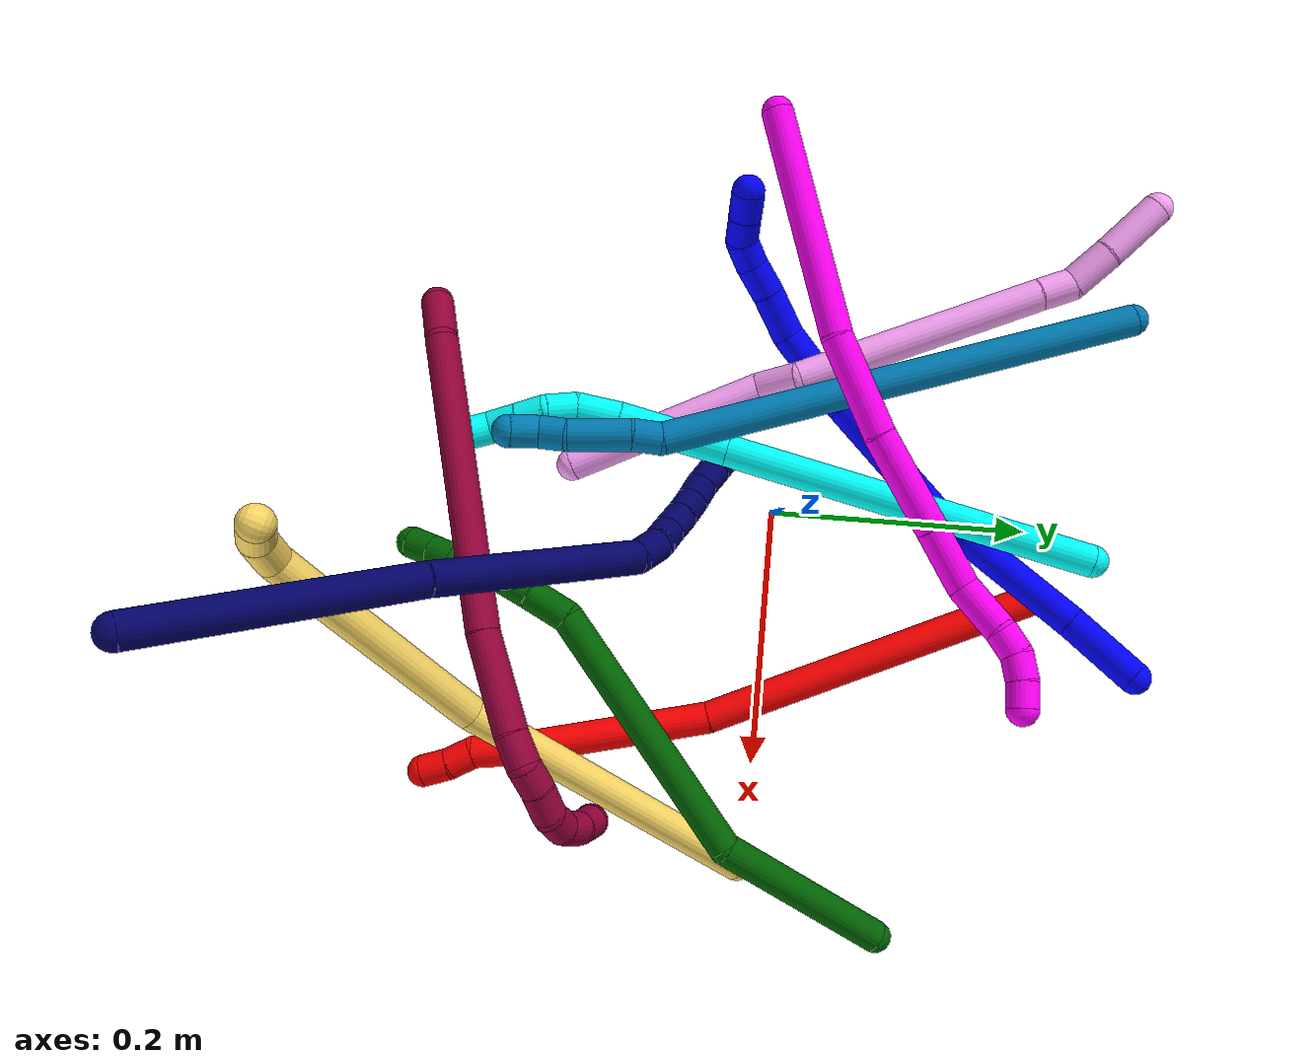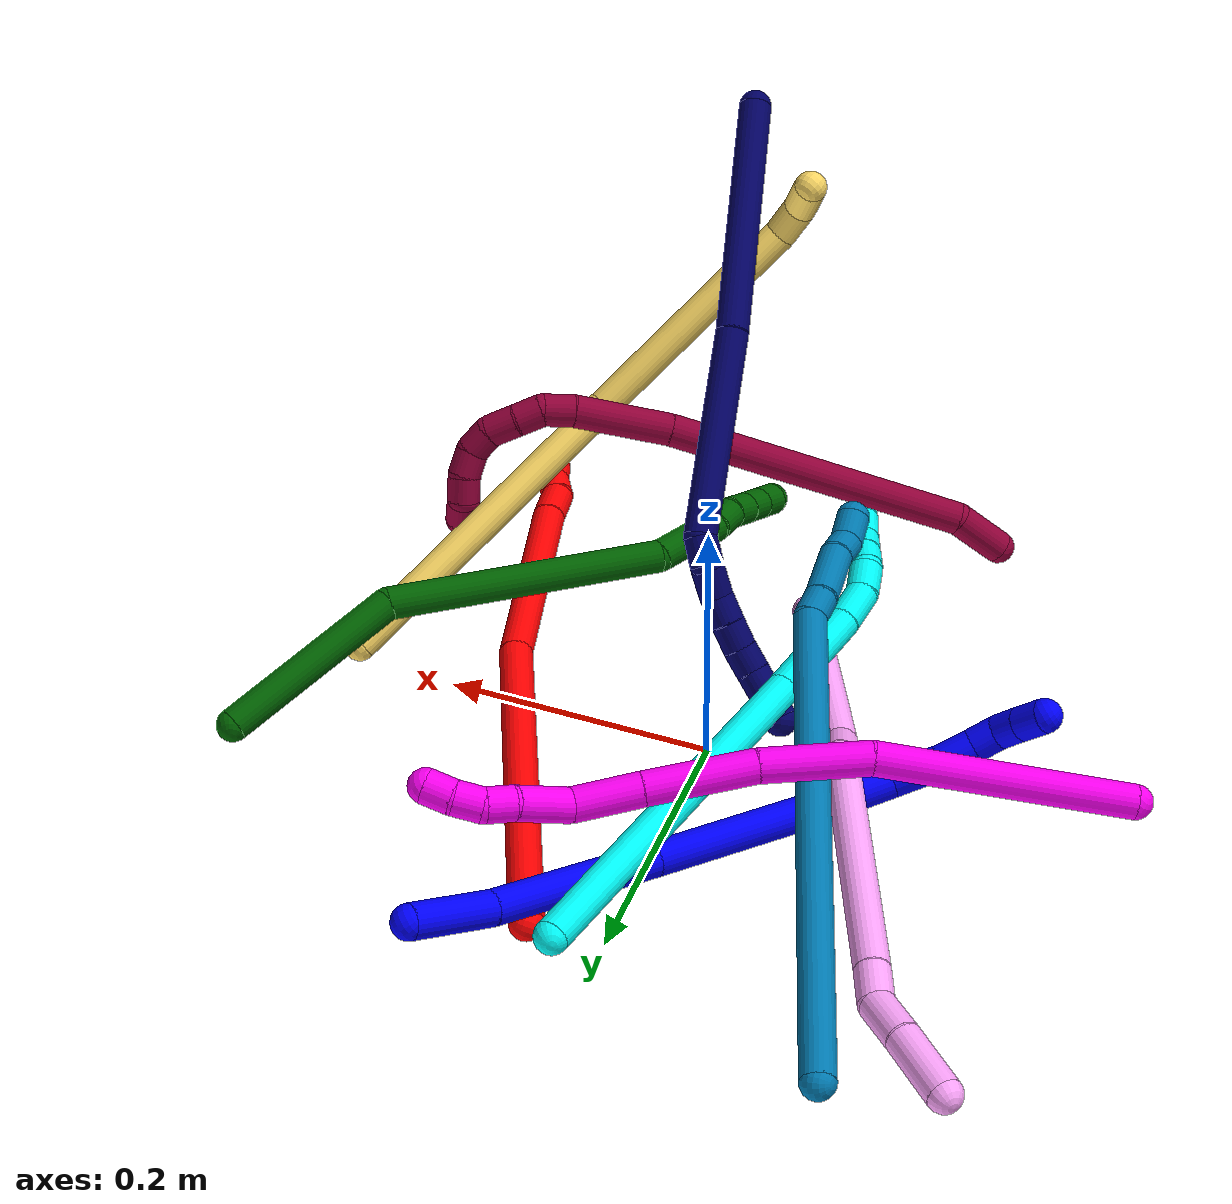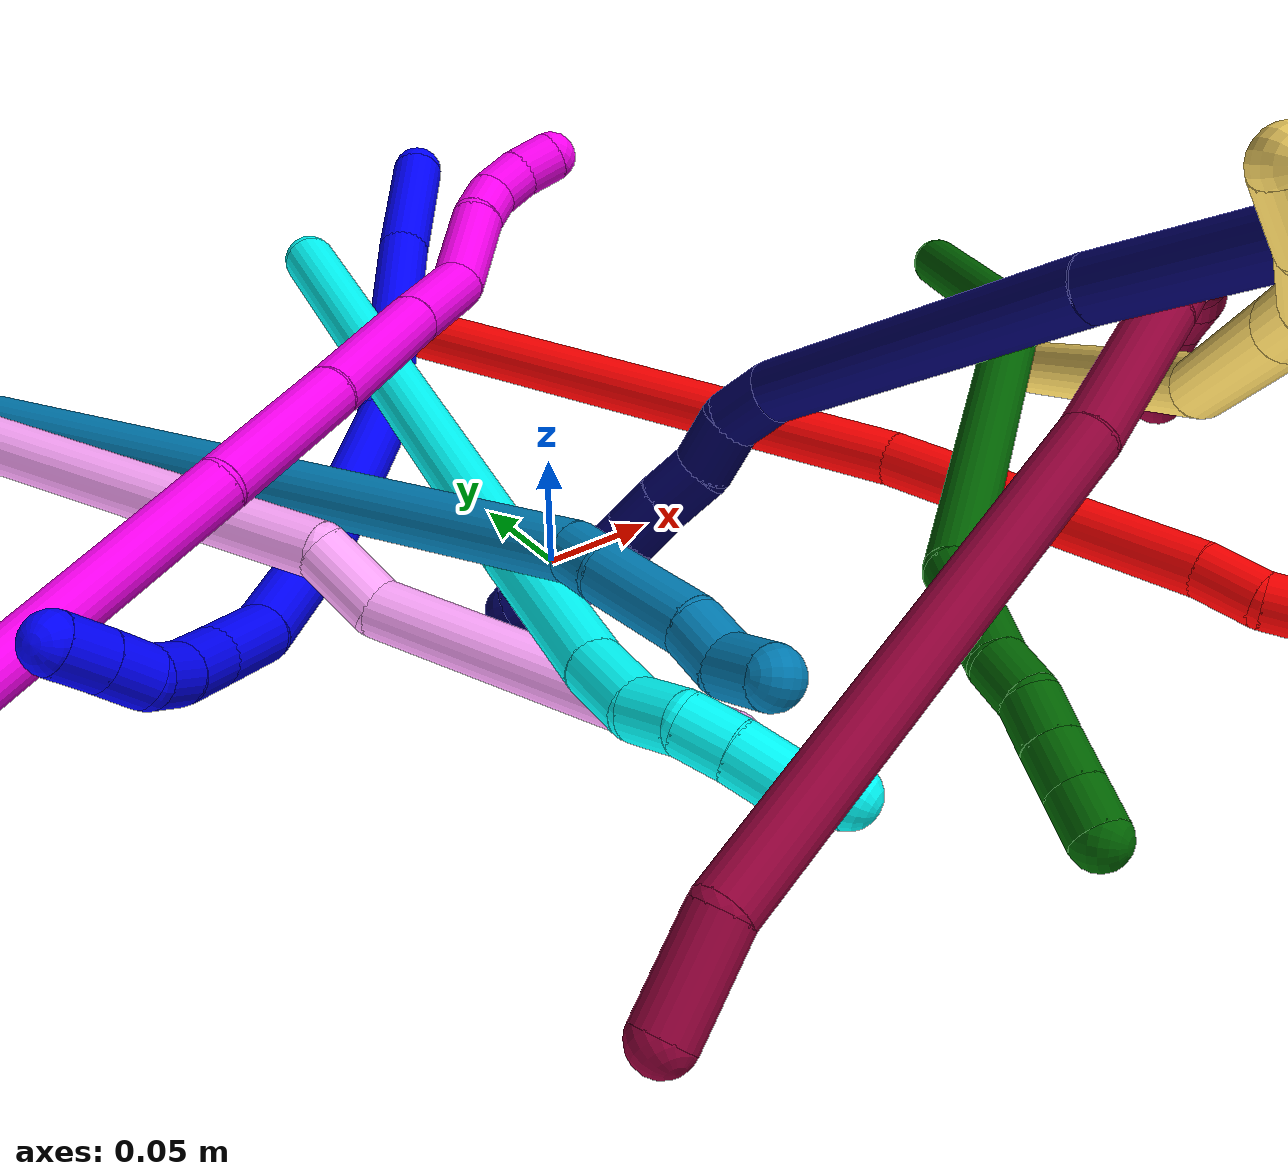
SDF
<sdf version="1.7">
 <world name="default">
  <plugin name="TubeGeneratorPlugin" filename="libtube_generator_plugin.so"/>
  <model name="photoneo_s_sensor">
   <static>1</static>
   <pose>0 0 2 1.57079 1.57079 3.14159</pose>
   <link name="link">
    <inertial><mass>0.1</mass></inertial>
    <sensor name="sensor" type="depth">
     <update_rate>30</update_rate>
     <camera>
      <horizontal_fov>1.22</horizontal_fov>
      <image><width>1920</width><height>1200</height><format>B8G8R8</format></image>
      <clip><near>0.1</near><far>2</far></clip>
      <depth_camera><output>points</output></depth_camera>
     </camera>
     <plugin name="camera_plugin" filename="libgazebo_ros_depth_camera.so">
      <baseline>0.2</baseline>
      <alwaysOn>1</alwaysOn>
      <updateRate>0.0</updateRate>
      <cameraName>camera_ir</cameraName>
      <imageTopicName>/camera/color/image_raw</imageTopicName>
      <cameraInfoTopicName>/camera/color/camera_info</cameraInfoTopicName>
      <depthImageTopicName>/camera/depth/image_raw</depthImageTopicName>
      <depthImageCameraInfoTopicName>/camera/depth/camera_info</depthImageCameraInfoTopicName>
      <pointCloudTopicName>/camera/depth/points</pointCloudTopicName>
      <frameName>fr_optical</frameName>
      <pointCloudCutoff>0.1</pointCloudCutoff>
      <pointCloudCutoffMax>2.0</pointCloudCutoffMax>
      <distortionK1>0</distortionK1>
      <distortionK2>0</distortionK2>
      <distortionK3>0</distortionK3>
      <distortionT1>0</distortionT1>
      <distortionT2>0</distortionT2>
      <CxPrime>0</CxPrime>
      <Cx>0</Cx>
      <Cy>0</Cy>
      <focalLength>0</focalLength>
      <hackBaseline>0</hackBaseline>
     </plugin>
    </sensor>
   </link>
  </model>
  <gravity>0 0 -9.8</gravity>
  <magnetic_field>6e-06 2.3e-05 -4.2e-05</magnetic_field>
  <atmosphere type="adiabatic"/>
  <physics name="default_physics" default="0" type="ode">
   <max_step_size>0.003</max_step_size>
   <real_time_factor>1</real_time_factor>
   <real_time_update_rate>1000</real_time_update_rate>
   <max_contacts>10000</max_contacts>
   <ode>
    <solver>
     <type>quick</type>
     <iters>100</iters>
     <sor>1.3</sor>
     <use_dynamic_moi_rescaling>0</use_dynamic_moi_rescaling>
    </solver>
    <constraints>
     <contact_max_correcting_vel>0</contact_max_correcting_vel>
     <contact_surface_layer>0.001</contact_surface_layer>
     <cfm>0</cfm>
     <erp>0.2</erp>
    </constraints>
   </ode>
  </physics>
  <scene><ambient>0.4 0.4 0.4 1</ambient><background>0.7 0.7 0.7 1</background><shadows>0</shadows></scene>
  <audio><device>default</device></audio>
  <spherical_coordinates>
   <surface_model>EARTH_WGS84</surface_model>
   <latitude_deg>0</latitude_deg>
   <longitude_deg>0</longitude_deg>
   <elevation>0</elevation>
   <heading_deg>0</heading_deg>
  </spherical_coordinates>
  <model name="bin">
   <static>1</static>
   <link name="bottom">
    <collision name="collision-bottom">
     <pose>0 0 -0.01 0 -0 0</pose>
     <geometry><box><size>0.8 0.6 0.02</size></box></geometry>
     <surface>
      <friction><ode><mu>100</mu><mu2>100</mu2></ode></friction>
      <contact><collide_bitmask>65535</collide_bitmask></contact>
     </surface>
    </collision>
   </link>
   <link name="west_wall">
    <collision name="collision-west_wall">
     <pose>-0.41 0 0.1 0 -0 0</pose>
     <geometry><box><size>0.02 0.6 0.2</size></box></geometry>
     <surface>
      <friction><ode><mu>100</mu><mu2>100</mu2></ode></friction>
      <contact><collide_bitmask>65535</collide_bitmask></contact>
     </surface>
    </collision>
   </link>
   <link name="east_wall">
    <collision name="collision-east_wall">
     <pose>0.41 0 0.1 0 -0 0</pose>
     <geometry><box><size>0.02 0.6 0.2</size></box></geometry>
     <surface>
      <friction><ode><mu>100</mu><mu2>100</mu2></ode></friction>
      <contact><collide_bitmask>65535</collide_bitmask></contact>
     </surface>
    </collision>
   </link>
   <link name="south_wall">
    <collision name="collision-south_wall">
     <pose>0 -0.31 0.1 0 -0 0</pose>
     <geometry><box><size>0.8 0.02 0.2</size></box></geometry>
     <surface>
      <friction><ode><mu>100</mu><mu2>100</mu2></ode></friction>
      <contact><collide_bitmask>65535</collide_bitmask></contact>
     </surface>
    </collision>
   </link>
   <link name="north_wall">
    <collision name="collision-north_wall">
     <pose>0 0.31 0.1 0 -0 0</pose>
     <geometry><box><size>0.8 0.02 0.2</size></box></geometry>
     <surface>
      <friction><ode><mu>100</mu><mu2>100</mu2></ode></friction>
      <contact><collide_bitmask>65535</collide_bitmask></contact>
     </surface>
    </collision>
   </link>
  </model>
  <model name="1">
   <static>0</static>
   <link name="1">
    <collision name="collision-cylinder-e_1_1_4">
     <pose>-0.020033 -0.014274 -0.018842 2.49329 -0.703025 -1.65822</pose>
     <geometry><cylinder><radius>0.0125</radius><length>0.061971</length></cylinder></geometry>
     <surface>
      <friction><ode><mu>1.16</mu><mu2>1.16</mu2><slip1>0</slip1><slip2>0</slip2></ode></friction>
      <contact><ode><kp>1e+06</kp><kd>1</kd><max_vel>0</max_vel><min_depth>0.001</min_depth></ode></contact>
     </surface>
    </collision>
    <visual name="visual-cylinder-e_1_1_4">
     <pose>-0.020033 -0.014274 -0.018842 2.49329 -0.703025 -1.65822</pose>
     <geometry><cylinder><radius>0.0125</radius><length>0.061971</length></cylinder></geometry>
     <material><ambient>0 0 1 1</ambient></material>
    </visual>
    <collision name="collision-cylinder-e_2_4_5">
     <pose>-0.083283 -0.052259 -0.080915 2.63991 -0.71969 -1.94578</pose>
     <geometry><cylinder><radius>0.0125</radius><length>0.131131</length></cylinder></geometry>
     <surface>
      <friction><ode><mu>1.16</mu><mu2>1.16</mu2><slip1>0</slip1><slip2>0</slip2></ode></friction>
      <contact><ode><kp>1e+06</kp><kd>1</kd><max_vel>0</max_vel><min_depth>0.001</min_depth></ode></contact>
     </surface>
    </collision>
    <visual name="visual-cylinder-e_2_4_5">
     <pose>-0.083283 -0.052259 -0.080915 2.63991 -0.71969 -1.94578</pose>
     <geometry><cylinder><radius>0.0125</radius><length>0.131131</length></cylinder></geometry>
     <material><ambient>0 0 1 1</ambient></material>
    </visual>
    <collision name="collision-cylinder-e_3_5_6">
     <pose>-0.15321 -0.09425 -0.169335 2.75718 -0.501236 -1.84162</pose>
     <geometry><cylinder><radius>0.0125</radius><length>0.111169</length></cylinder></geometry>
     <surface>
      <friction><ode><mu>1.16</mu><mu2>1.16</mu2><slip1>0</slip1><slip2>0</slip2></ode></friction>
      <contact><ode><kp>1e+06</kp><kd>1</kd><max_vel>0</max_vel><min_depth>0.001</min_depth></ode></contact>
     </surface>
    </collision>
    <visual name="visual-cylinder-e_3_5_6">
     <pose>-0.15321 -0.09425 -0.169335 2.75718 -0.501236 -1.84162</pose>
     <geometry><cylinder><radius>0.0125</radius><length>0.111169</length></cylinder></geometry>
     <material><ambient>0 0 1 1</ambient></material>
    </visual>
    <collision name="collision-cylinder-e_4_6_7">
     <pose>-0.193377 -0.122099 -0.245818 2.84489 -0.390188 -1.84655</pose>
     <geometry><cylinder><radius>0.0125</radius><length>0.070766</length></cylinder></geometry>
     <surface>
      <friction><ode><mu>1.16</mu><mu2>1.16</mu2><slip1>0</slip1><slip2>0</slip2></ode></friction>
      <contact><ode><kp>1e+06</kp><kd>1</kd><max_vel>0</max_vel><min_depth>0.001</min_depth></ode></contact>
     </surface>
    </collision>
    <visual name="visual-cylinder-e_4_6_7">
     <pose>-0.193377 -0.122099 -0.245818 2.84489 -0.390188 -1.84655</pose>
     <geometry><cylinder><radius>0.0125</radius><length>0.070766</length></cylinder></geometry>
     <material><ambient>0 0 1 1</ambient></material>
    </visual>
    <collision name="collision-cylinder-e_5_7_8">
     <pose>-0.209117 -0.135366 -0.294844 2.9359 -0.125306 -1.09232</pose>
     <geometry><cylinder><radius>0.0125</radius><length>0.036515</length></cylinder></geometry>
     <surface>
      <friction><ode><mu>1.16</mu><mu2>1.16</mu2><slip1>0</slip1><slip2>0</slip2></ode></friction>
      <contact><ode><kp>1e+06</kp><kd>1</kd><max_vel>0</max_vel><min_depth>0.001</min_depth></ode></contact>
     </surface>
    </collision>
    <visual name="visual-cylinder-e_5_7_8">
     <pose>-0.209117 -0.135366 -0.294844 2.9359 -0.125306 -1.09232</pose>
     <geometry><cylinder><radius>0.0125</radius><length>0.036515</length></cylinder></geometry>
     <material><ambient>0 0 1 1</ambient></material>
    </visual>
    <collision name="collision-cylinder-e_6_8_9">
     <pose>-0.21348 -0.140431 -0.325563 3.03683 -0.15802 -1.97179</pose>
     <geometry><cylinder><radius>0.0125</radius><length>0.026447</length></cylinder></geometry>
     <surface>
      <friction><ode><mu>1.16</mu><mu2>1.16</mu2><slip1>0</slip1><slip2>0</slip2></ode></friction>
      <contact><ode><kp>1e+06</kp><kd>1</kd><max_vel>0</max_vel><min_depth>0.001</min_depth></ode></contact>
     </surface>
    </collision>
    <visual name="visual-cylinder-e_6_8_9">
     <pose>-0.21348 -0.140431 -0.325563 3.03683 -0.15802 -1.97179</pose>
     <geometry><cylinder><radius>0.0125</radius><length>0.026447</length></cylinder></geometry>
     <material><ambient>0 0 1 1</ambient></material>
    </visual>
    <collision name="collision-cylinder-e_7_9_10">
     <pose>-0.215477 -0.14206 -0.348834 3.116 0.008103 0.613184</pose>
     <geometry><cylinder><radius>0.0125</radius><length>0.020575</length></cylinder></geometry>
     <surface>
      <friction><ode><mu>1.16</mu><mu2>1.16</mu2><slip1>0</slip1><slip2>0</slip2></ode></friction>
      <contact><ode><kp>1e+06</kp><kd>1</kd><max_vel>0</max_vel><min_depth>0.001</min_depth></ode></contact>
     </surface>
    </collision>
    <visual name="visual-cylinder-e_7_9_10">
     <pose>-0.215477 -0.14206 -0.348834 3.116 0.008103 0.613184</pose>
     <geometry><cylinder><radius>0.0125</radius><length>0.020575</length></cylinder></geometry>
     <material><ambient>0 0 1 1</ambient></material>
    </visual>
    <collision name="collision-cylinder-e_8_10_11">
     <pose>-0.21035 -0.142413 -0.367887 3.13135 0.521946 3.10323</pose>
     <geometry><cylinder><radius>0.0125</radius><length>0.020233</length></cylinder></geometry>
     <surface>
      <friction><ode><mu>1.16</mu><mu2>1.16</mu2><slip1>0</slip1><slip2>0</slip2></ode></friction>
      <contact><ode><kp>1e+06</kp><kd>1</kd><max_vel>0</max_vel><min_depth>0.001</min_depth></ode></contact>
     </surface>
    </collision>
    <visual name="visual-cylinder-e_8_10_11">
     <pose>-0.21035 -0.142413 -0.367887 3.13135 0.521946 3.10323</pose>
     <geometry><cylinder><radius>0.0125</radius><length>0.020233</length></cylinder></geometry>
     <material><ambient>0 0 1 1</ambient></material>
    </visual>
    <collision name="collision-cylinder-e_9_11_2">
     <pose>-0.200061 -0.142861 -0.385857 3.10267 0.517857 2.99489</pose>
     <geometry><cylinder><radius>0.0125</radius><length>0.021193</length></cylinder></geometry>
     <surface>
      <friction><ode><mu>1.16</mu><mu2>1.16</mu2><slip1>0</slip1><slip2>0</slip2></ode></friction>
      <contact><ode><kp>1e+06</kp><kd>1</kd><max_vel>0</max_vel><min_depth>0.001</min_depth></ode></contact>
     </surface>
    </collision>
    <visual name="visual-cylinder-e_9_11_2">
     <pose>-0.200061 -0.142861 -0.385857 3.10267 0.517857 2.99489</pose>
     <geometry><cylinder><radius>0.0125</radius><length>0.021193</length></cylinder></geometry>
     <material><ambient>0 0 1 1</ambient></material>
    </visual>
    <collision name="collision-sphere-2">
     <pose>-0.194815 -0.143219 -0.395057 0 -0 0</pose>
     <geometry><sphere><radius>0.0125</radius></sphere></geometry>
     <surface>
      <friction><ode><mu>1.16</mu><mu2>1.16</mu2><slip1>0</slip1><slip2>0</slip2></ode></friction>
      <contact><ode><kp>1e+06</kp><kd>1</kd><max_vel>0</max_vel><min_depth>0.001</min_depth></ode></contact>
     </surface>
    </collision>
    <visual name="visual-sphere-2">
     <pose>-0.194815 -0.143219 -0.395057 0 -0 0</pose>
     <geometry><sphere><radius>0.0125</radius></sphere></geometry>
     <material><ambient>0 0 1 1</ambient></material>
    </visual>
    <collision name="collision-sphere-11">
     <pose>-0.205306 -0.142503 -0.376656 0 -0 0</pose>
     <geometry><sphere><radius>0.0125</radius></sphere></geometry>
     <surface>
      <friction><ode><mu>1.16</mu><mu2>1.16</mu2><slip1>0</slip1><slip2>0</slip2></ode></friction>
      <contact><ode><kp>1e+06</kp><kd>1</kd><max_vel>0</max_vel><min_depth>0.001</min_depth></ode></contact>
     </surface>
    </collision>
    <visual name="visual-sphere-11">
     <pose>-0.205306 -0.142503 -0.376656 0 -0 0</pose>
     <geometry><sphere><radius>0.0125</radius></sphere></geometry>
     <material><ambient>0 0 1 1</ambient></material>
    </visual>
    <collision name="collision-sphere-10">
     <pose>-0.215394 -0.142323 -0.359118 0 -0 0</pose>
     <geometry><sphere><radius>0.0125</radius></sphere></geometry>
     <surface>
      <friction><ode><mu>1.16</mu><mu2>1.16</mu2><slip1>0</slip1><slip2>0</slip2></ode></friction>
      <contact><ode><kp>1e+06</kp><kd>1</kd><max_vel>0</max_vel><min_depth>0.001</min_depth></ode></contact>
     </surface>
    </collision>
    <visual name="visual-sphere-10">
     <pose>-0.215394 -0.142323 -0.359118 0 -0 0</pose>
     <geometry><sphere><radius>0.0125</radius></sphere></geometry>
     <material><ambient>0 0 1 1</ambient></material>
    </visual>
    <collision name="collision-sphere-9">
     <pose>-0.215561 -0.141797 -0.338551 0 -0 0</pose>
     <geometry><sphere><radius>0.0125</radius></sphere></geometry>
     <surface>
      <friction><ode><mu>1.16</mu><mu2>1.16</mu2><slip1>0</slip1><slip2>0</slip2></ode></friction>
      <contact><ode><kp>1e+06</kp><kd>1</kd><max_vel>0</max_vel><min_depth>0.001</min_depth></ode></contact>
     </surface>
    </collision>
    <visual name="visual-sphere-9">
     <pose>-0.215561 -0.141797 -0.338551 0 -0 0</pose>
     <geometry><sphere><radius>0.0125</radius></sphere></geometry>
     <material><ambient>0 0 1 1</ambient></material>
    </visual>
    <collision name="collision-sphere-4">
     <pose>-0.040066 -0.028548 -0.037685 0 -0 0</pose>
     <geometry><sphere><radius>0.0125</radius></sphere></geometry>
     <surface>
      <friction><ode><mu>1.16</mu><mu2>1.16</mu2><slip1>0</slip1><slip2>0</slip2></ode></friction>
      <contact><ode><kp>1e+06</kp><kd>1</kd><max_vel>0</max_vel><min_depth>0.001</min_depth></ode></contact>
     </surface>
    </collision>
    <visual name="visual-sphere-4">
     <pose>-0.040066 -0.028548 -0.037685 0 -0 0</pose>
     <geometry><sphere><radius>0.0125</radius></sphere></geometry>
     <material><ambient>0 0 1 1</ambient></material>
    </visual>
    <collision name="collision-sphere-1">
     <geometry><sphere><radius>0.0125</radius></sphere></geometry>
     <surface>
      <friction><ode><mu>1.16</mu><mu2>1.16</mu2><slip1>0</slip1><slip2>0</slip2></ode></friction>
      <contact><ode><kp>1e+06</kp><kd>1</kd><max_vel>0</max_vel><min_depth>0.001</min_depth></ode></contact>
     </surface>
    </collision>
    <visual name="visual-sphere-1">
     <geometry><sphere><radius>0.0125</radius></sphere></geometry>
     <material><ambient>0 0 1 1</ambient></material>
    </visual>
    <collision name="collision-sphere-8">
     <pose>-0.211399 -0.139066 -0.312576 0 -0 0</pose>
     <geometry><sphere><radius>0.0125</radius></sphere></geometry>
     <surface>
      <friction><ode><mu>1.16</mu><mu2>1.16</mu2><slip1>0</slip1><slip2>0</slip2></ode></friction>
      <contact><ode><kp>1e+06</kp><kd>1</kd><max_vel>0</max_vel><min_depth>0.001</min_depth></ode></contact>
     </surface>
    </collision>
    <visual name="visual-sphere-8">
     <pose>-0.211399 -0.139066 -0.312576 0 -0 0</pose>
     <geometry><sphere><radius>0.0125</radius></sphere></geometry>
     <material><ambient>0 0 1 1</ambient></material>
    </visual>
    <collision name="collision-sphere-5">
     <pose>-0.126501 -0.07597 -0.124145 0 -0 0</pose>
     <geometry><sphere><radius>0.0125</radius></sphere></geometry>
     <surface>
      <friction><ode><mu>1.16</mu><mu2>1.16</mu2><slip1>0</slip1><slip2>0</slip2></ode></friction>
      <contact><ode><kp>1e+06</kp><kd>1</kd><max_vel>0</max_vel><min_depth>0.001</min_depth></ode></contact>
     </surface>
    </collision>
    <visual name="visual-sphere-5">
     <pose>-0.126501 -0.07597 -0.124145 0 -0 0</pose>
     <geometry><sphere><radius>0.0125</radius></sphere></geometry>
     <material><ambient>0 0 1 1</ambient></material>
    </visual>
    <collision name="collision-sphere-6">
     <pose>-0.179919 -0.112531 -0.214524 0 -0 0</pose>
     <geometry><sphere><radius>0.0125</radius></sphere></geometry>
     <surface>
      <friction><ode><mu>1.16</mu><mu2>1.16</mu2><slip1>0</slip1><slip2>0</slip2></ode></friction>
      <contact><ode><kp>1e+06</kp><kd>1</kd><max_vel>0</max_vel><min_depth>0.001</min_depth></ode></contact>
     </surface>
    </collision>
    <visual name="visual-sphere-6">
     <pose>-0.179919 -0.112531 -0.214524 0 -0 0</pose>
     <geometry><sphere><radius>0.0125</radius></sphere></geometry>
     <material><ambient>0 0 1 1</ambient></material>
    </visual>
    <collision name="collision-sphere-7">
     <pose>-0.206835 -0.131666 -0.277111 0 -0 0</pose>
     <geometry><sphere><radius>0.0125</radius></sphere></geometry>
     <surface>
      <friction><ode><mu>1.16</mu><mu2>1.16</mu2><slip1>0</slip1><slip2>0</slip2></ode></friction>
      <contact><ode><kp>1e+06</kp><kd>1</kd><max_vel>0</max_vel><min_depth>0.001</min_depth></ode></contact>
     </surface>
    </collision>
    <visual name="visual-sphere-7">
     <pose>-0.206835 -0.131666 -0.277111 0 -0 0</pose>
     <geometry><sphere><radius>0.0125</radius></sphere></geometry>
     <material><ambient>0 0 1 1</ambient></material>
    </visual>
    <inertial>
     <pose>-0.138181 -0.088689 -0.180346 0 -0 0</pose>
     <mass>0.5</mass>
     <inertia>
      <ixx>-0.000393</ixx>
      <ixy>0</ixy>
      <ixz>0</ixz>
      <iyy>-0.000107</iyy>
      <iyz>0</iyz>
      <izz>0.000309</izz>
     </inertia>
    </inertial>
   </link>
   <pose>0.103023 0.278502 0.062443 2.1897 -0.462653 1.82035</pose>
  </model>
  <model name="2">
   <static>0</static>
   <link name="2">
    <collision name="collision-cylinder-e_1_1_4">
     <pose>0.051498 -0.124496 0.017144 1.43395 0.388915 0.340052</pose>
     <geometry><cylinder><radius>0.0125</radius><length>0.271627</length></cylinder></geometry>
     <surface>
      <friction><ode><mu>1.16</mu><mu2>1.16</mu2><slip1>0</slip1><slip2>0</slip2></ode></friction>
      <contact><ode><kp>1e+06</kp><kd>1</kd><max_vel>0</max_vel><min_depth>0.001</min_depth></ode></contact>
     </surface>
    </collision>
    <visual name="visual-cylinder-e_1_1_4">
     <pose>0.051498 -0.124496 0.017144 1.43395 0.388915 0.340052</pose>
     <geometry><cylinder><radius>0.0125</radius><length>0.271627</length></cylinder></geometry>
     <material><ambient>1 0 0 1</ambient></material>
    </visual>
    <collision name="collision-cylinder-e_2_4_5">
     <pose>0.125122 -0.324034 0.031352 1.6099 0.286512 0.297776</pose>
     <geometry><cylinder><radius>0.0125</radius><length>0.156581</length></cylinder></geometry>
     <surface>
      <friction><ode><mu>1.16</mu><mu2>1.16</mu2><slip1>0</slip1><slip2>0</slip2></ode></friction>
      <contact><ode><kp>1e+06</kp><kd>1</kd><max_vel>0</max_vel><min_depth>0.001</min_depth></ode></contact>
     </surface>
    </collision>
    <visual name="visual-cylinder-e_2_4_5">
     <pose>0.125122 -0.324034 0.031352 1.6099 0.286512 0.297776</pose>
     <geometry><cylinder><radius>0.0125</radius><length>0.156581</length></cylinder></geometry>
     <material><ambient>1 0 0 1</ambient></material>
    </visual>
    <collision name="collision-cylinder-e_3_5_6">
     <pose>0.151898 -0.412584 0.026253 1.72962 0.327641 0.383017</pose>
     <geometry><cylinder><radius>0.0125</radius><length>0.028898</length></cylinder></geometry>
     <surface>
      <friction><ode><mu>1.16</mu><mu2>1.16</mu2><slip1>0</slip1><slip2>0</slip2></ode></friction>
      <contact><ode><kp>1e+06</kp><kd>1</kd><max_vel>0</max_vel><min_depth>0.001</min_depth></ode></contact>
     </surface>
    </collision>
    <visual name="visual-cylinder-e_3_5_6">
     <pose>0.151898 -0.412584 0.026253 1.72962 0.327641 0.383017</pose>
     <geometry><cylinder><radius>0.0125</radius><length>0.028898</length></cylinder></geometry>
     <material><ambient>1 0 0 1</ambient></material>
    </visual>
    <collision name="collision-cylinder-e_4_6_7">
     <pose>0.16137 -0.435202 0.026253 1.33757 0.475612 0.378528</pose>
     <geometry><cylinder><radius>0.0125</radius><length>0.021064</length></cylinder></geometry>
     <surface>
      <friction><ode><mu>1.16</mu><mu2>1.16</mu2><slip1>0</slip1><slip2>0</slip2></ode></friction>
      <contact><ode><kp>1e+06</kp><kd>1</kd><max_vel>0</max_vel><min_depth>0.001</min_depth></ode></contact>
     </surface>
    </collision>
    <visual name="visual-cylinder-e_4_6_7">
     <pose>0.16137 -0.435202 0.026253 1.33757 0.475612 0.378528</pose>
     <geometry><cylinder><radius>0.0125</radius><length>0.021064</length></cylinder></geometry>
     <material><ambient>1 0 0 1</ambient></material>
    </visual>
    <collision name="collision-cylinder-e_5_7_2">
     <pose>0.171191 -0.454014 0.028487 1.56355 0.475646 0.472341</pose>
     <geometry><cylinder><radius>0.0125</radius><length>0.02183</length></cylinder></geometry>
     <surface>
      <friction><ode><mu>1.16</mu><mu2>1.16</mu2><slip1>0</slip1><slip2>0</slip2></ode></friction>
      <contact><ode><kp>1e+06</kp><kd>1</kd><max_vel>0</max_vel><min_depth>0.001</min_depth></ode></contact>
     </surface>
    </collision>
    <visual name="visual-cylinder-e_5_7_2">
     <pose>0.171191 -0.454014 0.028487 1.56355 0.475646 0.472341</pose>
     <geometry><cylinder><radius>0.0125</radius><length>0.02183</length></cylinder></geometry>
     <material><ambient>1 0 0 1</ambient></material>
    </visual>
    <collision name="collision-sphere-2">
     <pose>0.176189 -0.463717 0.028558 0 -0 0</pose>
     <geometry><sphere><radius>0.0125</radius></sphere></geometry>
     <surface>
      <friction><ode><mu>1.16</mu><mu2>1.16</mu2><slip1>0</slip1><slip2>0</slip2></ode></friction>
      <contact><ode><kp>1e+06</kp><kd>1</kd><max_vel>0</max_vel><min_depth>0.001</min_depth></ode></contact>
     </surface>
    </collision>
    <visual name="visual-sphere-2">
     <pose>0.176189 -0.463717 0.028558 0 -0 0</pose>
     <geometry><sphere><radius>0.0125</radius></sphere></geometry>
     <material><ambient>1 0 0 1</ambient></material>
    </visual>
    <collision name="collision-sphere-7">
     <pose>0.166192 -0.444311 0.028417 0 -0 0</pose>
     <geometry><sphere><radius>0.0125</radius></sphere></geometry>
     <surface>
      <friction><ode><mu>1.16</mu><mu2>1.16</mu2><slip1>0</slip1><slip2>0</slip2></ode></friction>
      <contact><ode><kp>1e+06</kp><kd>1</kd><max_vel>0</max_vel><min_depth>0.001</min_depth></ode></contact>
     </surface>
    </collision>
    <visual name="visual-sphere-7">
     <pose>0.166192 -0.444311 0.028417 0 -0 0</pose>
     <geometry><sphere><radius>0.0125</radius></sphere></geometry>
     <material><ambient>1 0 0 1</ambient></material>
    </visual>
    <collision name="collision-sphere-6">
     <pose>0.156548 -0.426092 0.024089 0 -0 0</pose>
     <geometry><sphere><radius>0.0125</radius></sphere></geometry>
     <surface>
      <friction><ode><mu>1.16</mu><mu2>1.16</mu2><slip1>0</slip1><slip2>0</slip2></ode></friction>
      <contact><ode><kp>1e+06</kp><kd>1</kd><max_vel>0</max_vel><min_depth>0.001</min_depth></ode></contact>
     </surface>
    </collision>
    <visual name="visual-sphere-6">
     <pose>0.156548 -0.426092 0.024089 0 -0 0</pose>
     <geometry><sphere><radius>0.0125</radius></sphere></geometry>
     <material><ambient>1 0 0 1</ambient></material>
    </visual>
    <collision name="collision-sphere-5">
     <pose>0.147248 -0.399076 0.028416 0 -0 0</pose>
     <geometry><sphere><radius>0.0125</radius></sphere></geometry>
     <surface>
      <friction><ode><mu>1.16</mu><mu2>1.16</mu2><slip1>0</slip1><slip2>0</slip2></ode></friction>
      <contact><ode><kp>1e+06</kp><kd>1</kd><max_vel>0</max_vel><min_depth>0.001</min_depth></ode></contact>
     </surface>
    </collision>
    <visual name="visual-sphere-5">
     <pose>0.147248 -0.399076 0.028416 0 -0 0</pose>
     <geometry><sphere><radius>0.0125</radius></sphere></geometry>
     <material><ambient>1 0 0 1</ambient></material>
    </visual>
    <collision name="collision-sphere-1">
     <geometry><sphere><radius>0.0125</radius></sphere></geometry>
     <surface>
      <friction><ode><mu>1.16</mu><mu2>1.16</mu2><slip1>0</slip1><slip2>0</slip2></ode></friction>
      <contact><ode><kp>1e+06</kp><kd>1</kd><max_vel>0</max_vel><min_depth>0.001</min_depth></ode></contact>
     </surface>
    </collision>
    <visual name="visual-sphere-1">
     <geometry><sphere><radius>0.0125</radius></sphere></geometry>
     <material><ambient>1 0 0 1</ambient></material>
    </visual>
    <collision name="collision-sphere-4">
     <pose>0.102997 -0.248992 0.034288 0 -0 0</pose>
     <geometry><sphere><radius>0.0125</radius></sphere></geometry>
     <surface>
      <friction><ode><mu>1.16</mu><mu2>1.16</mu2><slip1>0</slip1><slip2>0</slip2></ode></friction>
      <contact><ode><kp>1e+06</kp><kd>1</kd><max_vel>0</max_vel><min_depth>0.001</min_depth></ode></contact>
     </surface>
    </collision>
    <visual name="visual-sphere-4">
     <pose>0.102997 -0.248992 0.034288 0 -0 0</pose>
     <geometry><sphere><radius>0.0125</radius></sphere></geometry>
     <material><ambient>1 0 0 1</ambient></material>
    </visual>
    <inertial>
     <pose>0.090212 -0.23111 0.022999 0 -0 0</pose>
     <mass>0.5</mass>
     <inertia>
      <ixx>0.002397</ixx>
      <ixy>0</ixy>
      <ixz>0</ixz>
      <iyy>0.001019</iyy>
      <iyz>0</iyz>
      <izz>0.001129</izz>
     </inertia>
    </inertial>
   </link>
   <pose>0.051796 0.209987 0.011499 -0.666381 1.05061 -0.443627</pose>
  </model>
  <model name="3">
   <static>0</static>
   <link name="3">
    <collision name="collision-cylinder-e_1_1_4">
     <pose>-0.023405 -0.08743 -0.113588 2.48559 -0.161854 -0.467945</pose>
     <geometry><cylinder><radius>0.0125</radius><length>0.290475</length></cylinder></geometry>
     <surface>
      <friction><ode><mu>1.16</mu><mu2>1.16</mu2><slip1>0</slip1><slip2>0</slip2></ode></friction>
      <contact><ode><kp>1e+06</kp><kd>1</kd><max_vel>0</max_vel><min_depth>0.001</min_depth></ode></contact>
     </surface>
    </collision>
    <visual name="visual-cylinder-e_1_1_4">
     <pose>-0.023405 -0.08743 -0.113588 2.48559 -0.161854 -0.467945</pose>
     <geometry><cylinder><radius>0.0125</radius><length>0.290475</length></cylinder></geometry>
     <material><ambient>0.003922 1 0.996078 1</ambient></material>
    </visual>
    <collision name="collision-cylinder-e_2_4_5">
     <pose>-0.05247 -0.201337 -0.260345 2.46792 -0.13259 -0.374742</pose>
     <geometry><cylinder><radius>0.0125</radius><length>0.085634</length></cylinder></geometry>
     <surface>
      <friction><ode><mu>1.16</mu><mu2>1.16</mu2><slip1>0</slip1><slip2>0</slip2></ode></friction>
      <contact><ode><kp>1e+06</kp><kd>1</kd><max_vel>0</max_vel><min_depth>0.001</min_depth></ode></contact>
     </surface>
    </collision>
    <visual name="visual-cylinder-e_2_4_5">
     <pose>-0.05247 -0.201337 -0.260345 2.46792 -0.13259 -0.374742</pose>
     <geometry><cylinder><radius>0.0125</radius><length>0.085634</length></cylinder></geometry>
     <material><ambient>0.003922 1 0.996078 1</ambient></material>
    </visual>
    <collision name="collision-cylinder-e_3_5_6">
     <pose>-0.058652 -0.237866 -0.306812 2.49434 -0.031261 -0.093141</pose>
     <geometry><cylinder><radius>0.0125</radius><length>0.033354</length></cylinder></geometry>
     <surface>
      <friction><ode><mu>1.16</mu><mu2>1.16</mu2><slip1>0</slip1><slip2>0</slip2></ode></friction>
      <contact><ode><kp>1e+06</kp><kd>1</kd><max_vel>0</max_vel><min_depth>0.001</min_depth></ode></contact>
     </surface>
    </collision>
    <visual name="visual-cylinder-e_3_5_6">
     <pose>-0.058652 -0.237866 -0.306812 2.49434 -0.031261 -0.093141</pose>
     <geometry><cylinder><radius>0.0125</radius><length>0.033354</length></cylinder></geometry>
     <material><ambient>0.003922 1 0.996078 1</ambient></material>
    </visual>
    <collision name="collision-cylinder-e_4_6_7">
     <pose>-0.055808 -0.253355 -0.330146 2.64508 0.286675 1.03518</pose>
     <geometry><cylinder><radius>0.0125</radius><length>0.023803</length></cylinder></geometry>
     <surface>
      <friction><ode><mu>1.16</mu><mu2>1.16</mu2><slip1>0</slip1><slip2>0</slip2></ode></friction>
      <contact><ode><kp>1e+06</kp><kd>1</kd><max_vel>0</max_vel><min_depth>0.001</min_depth></ode></contact>
     </surface>
    </collision>
    <visual name="visual-cylinder-e_4_6_7">
     <pose>-0.055808 -0.253355 -0.330146 2.64508 0.286675 1.03518</pose>
     <geometry><cylinder><radius>0.0125</radius><length>0.023803</length></cylinder></geometry>
     <material><ambient>0.003922 1 0.996078 1</ambient></material>
    </visual>
    <collision name="collision-cylinder-e_5_7_8">
     <pose>-0.05172 -0.259961 -0.350797 3.032 0.067494 1.10347</pose>
     <geometry><cylinder><radius>0.0125</radius><length>0.021404</length></cylinder></geometry>
     <surface>
      <friction><ode><mu>1.16</mu><mu2>1.16</mu2><slip1>0</slip1><slip2>0</slip2></ode></friction>
      <contact><ode><kp>1e+06</kp><kd>1</kd><max_vel>0</max_vel><min_depth>0.001</min_depth></ode></contact>
     </surface>
    </collision>
    <visual name="visual-cylinder-e_5_7_8">
     <pose>-0.05172 -0.259961 -0.350797 3.032 0.067494 1.10347</pose>
     <geometry><cylinder><radius>0.0125</radius><length>0.021404</length></cylinder></geometry>
     <material><ambient>0.003922 1 0.996078 1</ambient></material>
    </visual>
    <collision name="collision-cylinder-e_6_8_9">
     <pose>-0.051099 -0.262057 -0.3735 3.06495 -0.008308 -0.215844</pose>
     <geometry><cylinder><radius>0.0125</radius><length>0.024252</length></cylinder></geometry>
     <surface>
      <friction><ode><mu>1.16</mu><mu2>1.16</mu2><slip1>0</slip1><slip2>0</slip2></ode></friction>
      <contact><ode><kp>1e+06</kp><kd>1</kd><max_vel>0</max_vel><min_depth>0.001</min_depth></ode></contact>
     </surface>
    </collision>
    <visual name="visual-cylinder-e_6_8_9">
     <pose>-0.051099 -0.262057 -0.3735 3.06495 -0.008308 -0.215844</pose>
     <geometry><cylinder><radius>0.0125</radius><length>0.024252</length></cylinder></geometry>
     <material><ambient>0.003922 1 0.996078 1</ambient></material>
    </visual>
    <collision name="collision-cylinder-e_7_9_2">
     <pose>-0.046868 -0.266534 -0.394518 2.76324 0.423628 1.68666</pose>
     <geometry><cylinder><radius>0.0125</radius><length>0.021079</length></cylinder></geometry>
     <surface>
      <friction><ode><mu>1.16</mu><mu2>1.16</mu2><slip1>0</slip1><slip2>0</slip2></ode></friction>
      <contact><ode><kp>1e+06</kp><kd>1</kd><max_vel>0</max_vel><min_depth>0.001</min_depth></ode></contact>
     </surface>
    </collision>
    <visual name="visual-cylinder-e_7_9_2">
     <pose>-0.046868 -0.266534 -0.394518 2.76324 0.423628 1.68666</pose>
     <geometry><cylinder><radius>0.0125</radius><length>0.021079</length></cylinder></geometry>
     <material><ambient>0.003922 1 0.996078 1</ambient></material>
    </visual>
    <collision name="collision-sphere-2">
     <pose>-0.042535 -0.270083 -0.403447 0 -0 0</pose>
     <geometry><sphere><radius>0.0125</radius></sphere></geometry>
     <surface>
      <friction><ode><mu>1.16</mu><mu2>1.16</mu2><slip1>0</slip1><slip2>0</slip2></ode></friction>
      <contact><ode><kp>1e+06</kp><kd>1</kd><max_vel>0</max_vel><min_depth>0.001</min_depth></ode></contact>
     </surface>
    </collision>
    <visual name="visual-sphere-2">
     <pose>-0.042535 -0.270083 -0.403447 0 -0 0</pose>
     <geometry><sphere><radius>0.0125</radius></sphere></geometry>
     <material><ambient>0.003922 1 0.996078 1</ambient></material>
    </visual>
    <collision name="collision-sphere-9">
     <pose>-0.0512 -0.262985 -0.38559 0 -0 0</pose>
     <geometry><sphere><radius>0.0125</radius></sphere></geometry>
     <surface>
      <friction><ode><mu>1.16</mu><mu2>1.16</mu2><slip1>0</slip1><slip2>0</slip2></ode></friction>
      <contact><ode><kp>1e+06</kp><kd>1</kd><max_vel>0</max_vel><min_depth>0.001</min_depth></ode></contact>
     </surface>
    </collision>
    <visual name="visual-sphere-9">
     <pose>-0.0512 -0.262985 -0.38559 0 -0 0</pose>
     <geometry><sphere><radius>0.0125</radius></sphere></geometry>
     <material><ambient>0.003922 1 0.996078 1</ambient></material>
    </visual>
    <collision name="collision-sphere-4">
     <pose>-0.046809 -0.17486 -0.227175 0 -0 0</pose>
     <geometry><sphere><radius>0.0125</radius></sphere></geometry>
     <surface>
      <friction><ode><mu>1.16</mu><mu2>1.16</mu2><slip1>0</slip1><slip2>0</slip2></ode></friction>
      <contact><ode><kp>1e+06</kp><kd>1</kd><max_vel>0</max_vel><min_depth>0.001</min_depth></ode></contact>
     </surface>
    </collision>
    <visual name="visual-sphere-4">
     <pose>-0.046809 -0.17486 -0.227175 0 -0 0</pose>
     <geometry><sphere><radius>0.0125</radius></sphere></geometry>
     <material><ambient>0.003922 1 0.996078 1</ambient></material>
    </visual>
    <collision name="collision-sphere-1">
     <geometry><sphere><radius>0.0125</radius></sphere></geometry>
     <surface>
      <friction><ode><mu>1.16</mu><mu2>1.16</mu2><slip1>0</slip1><slip2>0</slip2></ode></friction>
      <contact><ode><kp>1e+06</kp><kd>1</kd><max_vel>0</max_vel><min_depth>0.001</min_depth></ode></contact>
     </surface>
    </collision>
    <visual name="visual-sphere-1">
     <geometry><sphere><radius>0.0125</radius></sphere></geometry>
     <material><ambient>0.003922 1 0.996078 1</ambient></material>
    </visual>
    <collision name="collision-sphere-8">
     <pose>-0.050999 -0.261129 -0.361411 0 -0 0</pose>
     <geometry><sphere><radius>0.0125</radius></sphere></geometry>
     <surface>
      <friction><ode><mu>1.16</mu><mu2>1.16</mu2><slip1>0</slip1><slip2>0</slip2></ode></friction>
      <contact><ode><kp>1e+06</kp><kd>1</kd><max_vel>0</max_vel><min_depth>0.001</min_depth></ode></contact>
     </surface>
    </collision>
    <visual name="visual-sphere-8">
     <pose>-0.050999 -0.261129 -0.361411 0 -0 0</pose>
     <geometry><sphere><radius>0.0125</radius></sphere></geometry>
     <material><ambient>0.003922 1 0.996078 1</ambient></material>
    </visual>
    <collision name="collision-sphere-5">
     <pose>-0.05813 -0.227814 -0.293514 0 -0 0</pose>
     <geometry><sphere><radius>0.0125</radius></sphere></geometry>
     <surface>
      <friction><ode><mu>1.16</mu><mu2>1.16</mu2><slip1>0</slip1><slip2>0</slip2></ode></friction>
      <contact><ode><kp>1e+06</kp><kd>1</kd><max_vel>0</max_vel><min_depth>0.001</min_depth></ode></contact>
     </surface>
    </collision>
    <visual name="visual-sphere-5">
     <pose>-0.05813 -0.227814 -0.293514 0 -0 0</pose>
     <geometry><sphere><radius>0.0125</radius></sphere></geometry>
     <material><ambient>0.003922 1 0.996078 1</ambient></material>
    </visual>
    <collision name="collision-sphere-6">
     <pose>-0.059173 -0.247917 -0.320109 0 -0 0</pose>
     <geometry><sphere><radius>0.0125</radius></sphere></geometry>
     <surface>
      <friction><ode><mu>1.16</mu><mu2>1.16</mu2><slip1>0</slip1><slip2>0</slip2></ode></friction>
      <contact><ode><kp>1e+06</kp><kd>1</kd><max_vel>0</max_vel><min_depth>0.001</min_depth></ode></contact>
     </surface>
    </collision>
    <visual name="visual-sphere-6">
     <pose>-0.059173 -0.247917 -0.320109 0 -0 0</pose>
     <geometry><sphere><radius>0.0125</radius></sphere></geometry>
     <material><ambient>0.003922 1 0.996078 1</ambient></material>
    </visual>
    <collision name="collision-sphere-7">
     <pose>-0.052442 -0.258793 -0.340184 0 -0 0</pose>
     <geometry><sphere><radius>0.0125</radius></sphere></geometry>
     <surface>
      <friction><ode><mu>1.16</mu><mu2>1.16</mu2><slip1>0</slip1><slip2>0</slip2></ode></friction>
      <contact><ode><kp>1e+06</kp><kd>1</kd><max_vel>0</max_vel><min_depth>0.001</min_depth></ode></contact>
     </surface>
    </collision>
    <visual name="visual-sphere-7">
     <pose>-0.052442 -0.258793 -0.340184 0 -0 0</pose>
     <geometry><sphere><radius>0.0125</radius></sphere></geometry>
     <material><ambient>0.003922 1 0.996078 1</ambient></material>
    </visual>
    <inertial>
     <pose>-0.035821 -0.148279 -0.196526 0 -0 0</pose>
     <mass>0.5</mass>
     <inertia>
      <ixx>0.000934</ixx>
      <ixy>0</ixy>
      <ixz>0</ixz>
      <iyy>-0.002359</iyy>
      <iyz>0</iyz>
      <izz>0.001581</izz>
     </inertia>
    </inertial>
   </link>
   <pose>0.018347 0.244225 0.046285 -1.1067 -0.946441 0.034007</pose>
  </model>
  <model name="4">
   <static>0</static>
   <link name="4">
    <collision name="collision-cylinder-e_1_1_4">
     <pose>-0.019416 -0.017457 0.07468 0.229638 -0.247956 -0.028741</pose>
     <geometry><cylinder><radius>0.0125</radius><length>0.158227</length></cylinder></geometry>
     <surface>
      <friction><ode><mu>1.16</mu><mu2>1.16</mu2><slip1>0</slip1><slip2>0</slip2></ode></friction>
      <contact><ode><kp>1e+06</kp><kd>1</kd><max_vel>0</max_vel><min_depth>0.001</min_depth></ode></contact>
     </surface>
    </collision>
    <visual name="visual-cylinder-e_1_1_4">
     <pose>-0.019416 -0.017457 0.07468 0.229638 -0.247956 -0.028741</pose>
     <geometry><cylinder><radius>0.0125</radius><length>0.158227</length></cylinder></geometry>
     <material><ambient>1 0.65098 0.996078 1</ambient></material>
    </visual>
    <collision name="collision-cylinder-e_2_4_5">
     <pose>-0.049396 -0.036466 0.162558 0.116972 -0.671687 -0.040872</pose>
     <geometry><cylinder><radius>0.0125</radius><length>0.03395</length></cylinder></geometry>
     <surface>
      <friction><ode><mu>1.16</mu><mu2>1.16</mu2><slip1>0</slip1><slip2>0</slip2></ode></friction>
      <contact><ode><kp>1e+06</kp><kd>1</kd><max_vel>0</max_vel><min_depth>0.001</min_depth></ode></contact>
     </surface>
    </collision>
    <visual name="visual-cylinder-e_2_4_5">
     <pose>-0.049396 -0.036466 0.162558 0.116972 -0.671687 -0.040872</pose>
     <geometry><cylinder><radius>0.0125</radius><length>0.03395</length></cylinder></geometry>
     <material><ambient>1 0.65098 0.996078 1</ambient></material>
    </visual>
    <collision name="collision-cylinder-e_3_5_6">
     <pose>-0.079249 -0.067755 0.266727 0.315944 -0.198872 -0.031782</pose>
     <geometry><cylinder><radius>0.0125</radius><length>0.195269</length></cylinder></geometry>
     <surface>
      <friction><ode><mu>1.16</mu><mu2>1.16</mu2><slip1>0</slip1><slip2>0</slip2></ode></friction>
      <contact><ode><kp>1e+06</kp><kd>1</kd><max_vel>0</max_vel><min_depth>0.001</min_depth></ode></contact>
     </surface>
    </collision>
    <visual name="visual-cylinder-e_3_5_6">
     <pose>-0.079249 -0.067755 0.266727 0.315944 -0.198872 -0.031782</pose>
     <geometry><cylinder><radius>0.0125</radius><length>0.195269</length></cylinder></geometry>
     <material><ambient>1 0.65098 0.996078 1</ambient></material>
    </visual>
    <collision name="collision-cylinder-e_4_6_7">
     <pose>-0.100642 -0.10224 0.370263 0.361247 -0.155393 -0.028432</pose>
     <geometry><cylinder><radius>0.0125</radius><length>0.027186</length></cylinder></geometry>
     <surface>
      <friction><ode><mu>1.16</mu><mu2>1.16</mu2><slip1>0</slip1><slip2>0</slip2></ode></friction>
      <contact><ode><kp>1e+06</kp><kd>1</kd><max_vel>0</max_vel><min_depth>0.001</min_depth></ode></contact>
     </surface>
    </collision>
    <visual name="visual-cylinder-e_4_6_7">
     <pose>-0.100642 -0.10224 0.370263 0.361247 -0.155393 -0.028432</pose>
     <geometry><cylinder><radius>0.0125</radius><length>0.027186</length></cylinder></geometry>
     <material><ambient>1 0.65098 0.996078 1</ambient></material>
    </visual>
    <collision name="collision-cylinder-e_5_7_8">
     <pose>-0.104785 -0.105585 0.400171 -0.080595 -0.116664 0.004709</pose>
     <geometry><cylinder><radius>0.0125</radius><length>0.035043</length></cylinder></geometry>
     <surface>
      <friction><ode><mu>1.16</mu><mu2>1.16</mu2><slip1>0</slip1><slip2>0</slip2></ode></friction>
      <contact><ode><kp>1e+06</kp><kd>1</kd><max_vel>0</max_vel><min_depth>0.001</min_depth></ode></contact>
     </surface>
    </collision>
    <visual name="visual-cylinder-e_5_7_8">
     <pose>-0.104785 -0.105585 0.400171 -0.080595 -0.116664 0.004709</pose>
     <geometry><cylinder><radius>0.0125</radius><length>0.035043</length></cylinder></geometry>
     <material><ambient>1 0.65098 0.996078 1</ambient></material>
    </visual>
    <collision name="collision-cylinder-e_6_8_2">
     <pose>-0.106705 -0.103159 0.442658 -0.040741 0.004745 -9.7e-05</pose>
     <geometry><cylinder><radius>0.0125</radius><length>0.050325</length></cylinder></geometry>
     <surface>
      <friction><ode><mu>1.16</mu><mu2>1.16</mu2><slip1>0</slip1><slip2>0</slip2></ode></friction>
      <contact><ode><kp>1e+06</kp><kd>1</kd><max_vel>0</max_vel><min_depth>0.001</min_depth></ode></contact>
     </surface>
    </collision>
    <visual name="visual-cylinder-e_6_8_2">
     <pose>-0.106705 -0.103159 0.442658 -0.040741 0.004745 -9.7e-05</pose>
     <geometry><cylinder><radius>0.0125</radius><length>0.050325</length></cylinder></geometry>
     <material><ambient>1 0.65098 0.996078 1</ambient></material>
    </visual>
    <collision name="collision-sphere-2">
     <pose>-0.106586 -0.102134 0.4678 0 -0 0</pose>
     <geometry><sphere><radius>0.0125</radius></sphere></geometry>
     <surface>
      <friction><ode><mu>1.16</mu><mu2>1.16</mu2><slip1>0</slip1><slip2>0</slip2></ode></friction>
      <contact><ode><kp>1e+06</kp><kd>1</kd><max_vel>0</max_vel><min_depth>0.001</min_depth></ode></contact>
     </surface>
    </collision>
    <visual name="visual-sphere-2">
     <pose>-0.106586 -0.102134 0.4678 0 -0 0</pose>
     <geometry><sphere><radius>0.0125</radius></sphere></geometry>
     <material><ambient>1 0.65098 0.996078 1</ambient></material>
    </visual>
    <collision name="collision-sphere-4">
     <pose>-0.038832 -0.034915 0.149361 0 -0 0</pose>
     <geometry><sphere><radius>0.0125</radius></sphere></geometry>
     <surface>
      <friction><ode><mu>1.16</mu><mu2>1.16</mu2><slip1>0</slip1><slip2>0</slip2></ode></friction>
      <contact><ode><kp>1e+06</kp><kd>1</kd><max_vel>0</max_vel><min_depth>0.001</min_depth></ode></contact>
     </surface>
    </collision>
    <visual name="visual-sphere-4">
     <pose>-0.038832 -0.034915 0.149361 0 -0 0</pose>
     <geometry><sphere><radius>0.0125</radius></sphere></geometry>
     <material><ambient>1 0.65098 0.996078 1</ambient></material>
    </visual>
    <collision name="collision-sphere-1">
     <geometry><sphere><radius>0.0125</radius></sphere></geometry>
     <surface>
      <friction><ode><mu>1.16</mu><mu2>1.16</mu2><slip1>0</slip1><slip2>0</slip2></ode></friction>
      <contact><ode><kp>1e+06</kp><kd>1</kd><max_vel>0</max_vel><min_depth>0.001</min_depth></ode></contact>
     </surface>
    </collision>
    <visual name="visual-sphere-1">
     <geometry><sphere><radius>0.0125</radius></sphere></geometry>
     <material><ambient>1 0.65098 0.996078 1</ambient></material>
    </visual>
    <collision name="collision-sphere-8">
     <pose>-0.106824 -0.104184 0.417517 0 -0 0</pose>
     <geometry><sphere><radius>0.0125</radius></sphere></geometry>
     <surface>
      <friction><ode><mu>1.16</mu><mu2>1.16</mu2><slip1>0</slip1><slip2>0</slip2></ode></friction>
      <contact><ode><kp>1e+06</kp><kd>1</kd><max_vel>0</max_vel><min_depth>0.001</min_depth></ode></contact>
     </surface>
    </collision>
    <visual name="visual-sphere-8">
     <pose>-0.106824 -0.104184 0.417517 0 -0 0</pose>
     <geometry><sphere><radius>0.0125</radius></sphere></geometry>
     <material><ambient>1 0.65098 0.996078 1</ambient></material>
    </visual>
    <collision name="collision-sphere-5">
     <pose>-0.05996 -0.038016 0.175754 0 -0 0</pose>
     <geometry><sphere><radius>0.0125</radius></sphere></geometry>
     <surface>
      <friction><ode><mu>1.16</mu><mu2>1.16</mu2><slip1>0</slip1><slip2>0</slip2></ode></friction>
      <contact><ode><kp>1e+06</kp><kd>1</kd><max_vel>0</max_vel><min_depth>0.001</min_depth></ode></contact>
     </surface>
    </collision>
    <visual name="visual-sphere-5">
     <pose>-0.05996 -0.038016 0.175754 0 -0 0</pose>
     <geometry><sphere><radius>0.0125</radius></sphere></geometry>
     <material><ambient>1 0.65098 0.996078 1</ambient></material>
    </visual>
    <collision name="collision-sphere-6">
     <pose>-0.098538 -0.097493 0.3577 0 -0 0</pose>
     <geometry><sphere><radius>0.0125</radius></sphere></geometry>
     <surface>
      <friction><ode><mu>1.16</mu><mu2>1.16</mu2><slip1>0</slip1><slip2>0</slip2></ode></friction>
      <contact><ode><kp>1e+06</kp><kd>1</kd><max_vel>0</max_vel><min_depth>0.001</min_depth></ode></contact>
     </surface>
    </collision>
    <visual name="visual-sphere-6">
     <pose>-0.098538 -0.097493 0.3577 0 -0 0</pose>
     <geometry><sphere><radius>0.0125</radius></sphere></geometry>
     <material><ambient>1 0.65098 0.996078 1</ambient></material>
    </visual>
    <collision name="collision-sphere-7">
     <pose>-0.102745 -0.106986 0.382825 0 -0 0</pose>
     <geometry><sphere><radius>0.0125</radius></sphere></geometry>
     <surface>
      <friction><ode><mu>1.16</mu><mu2>1.16</mu2><slip1>0</slip1><slip2>0</slip2></ode></friction>
      <contact><ode><kp>1e+06</kp><kd>1</kd><max_vel>0</max_vel><min_depth>0.001</min_depth></ode></contact>
     </surface>
    </collision>
    <visual name="visual-sphere-7">
     <pose>-0.102745 -0.106986 0.382825 0 -0 0</pose>
     <geometry><sphere><radius>0.0125</radius></sphere></geometry>
     <material><ambient>1 0.65098 0.996078 1</ambient></material>
    </visual>
    <inertial>
     <pose>-0.064004 -0.057803 0.23157 0 -0 0</pose>
     <mass>0.5</mass>
     <inertia>
      <ixx>0.000928</ixx>
      <ixy>0</ixy>
      <ixz>0</ixz>
      <iyy>0.000913</iyy>
      <iyz>0</iyz>
      <izz>0.000513</izz>
     </inertia>
    </inertial>
   </link>
   <pose>-0.024673 -0.15877 0.011704 1.59423 0.991962 -2.33573</pose>
  </model>
  <model name="5">
   <static>0</static>
   <link name="5">
    <collision name="collision-cylinder-e_1_1_4">
     <pose>-0.012917 -0.023691 0.12681 0.18469 -0.099799 -0.00925</pose>
     <geometry><cylinder><radius>0.0125</radius><length>0.259298</length></cylinder></geometry>
     <surface>
      <friction><ode><mu>1.16</mu><mu2>1.16</mu2><slip1>0</slip1><slip2>0</slip2></ode></friction>
      <contact><ode><kp>1e+06</kp><kd>1</kd><max_vel>0</max_vel><min_depth>0.001</min_depth></ode></contact>
     </surface>
    </collision>
    <visual name="visual-cylinder-e_1_1_4">
     <pose>-0.012917 -0.023691 0.12681 0.18469 -0.099799 -0.00925</pose>
     <geometry><cylinder><radius>0.0125</radius><length>0.259298</length></cylinder></geometry>
     <material><ambient>1 0.858824 0.4 1</ambient></material>
    </visual>
    <collision name="collision-cylinder-e_2_4_5">
     <pose>-0.04511 -0.071771 0.319924 0.352487 -0.266355 -0.047709</pose>
     <geometry><cylinder><radius>0.0125</radius><length>0.14646</length></cylinder></geometry>
     <surface>
      <friction><ode><mu>1.16</mu><mu2>1.16</mu2><slip1>0</slip1><slip2>0</slip2></ode></friction>
      <contact><ode><kp>1e+06</kp><kd>1</kd><max_vel>0</max_vel><min_depth>0.001</min_depth></ode></contact>
     </surface>
    </collision>
    <visual name="visual-cylinder-e_2_4_5">
     <pose>-0.04511 -0.071771 0.319924 0.352487 -0.266355 -0.047709</pose>
     <geometry><cylinder><radius>0.0125</radius><length>0.14646</length></cylinder></geometry>
     <material><ambient>1 0.858824 0.4 1</ambient></material>
    </visual>
    <collision name="collision-cylinder-e_3_5_6">
     <pose>-0.069685 -0.103036 0.404531 0.359304 -0.264705 -0.048346</pose>
     <geometry><cylinder><radius>0.0125</radius><length>0.040514</length></cylinder></geometry>
     <surface>
      <friction><ode><mu>1.16</mu><mu2>1.16</mu2><slip1>0</slip1><slip2>0</slip2></ode></friction>
      <contact><ode><kp>1e+06</kp><kd>1</kd><max_vel>0</max_vel><min_depth>0.001</min_depth></ode></contact>
     </surface>
    </collision>
    <visual name="visual-cylinder-e_3_5_6">
     <pose>-0.069685 -0.103036 0.404531 0.359304 -0.264705 -0.048346</pose>
     <geometry><cylinder><radius>0.0125</radius><length>0.040514</length></cylinder></geometry>
     <material><ambient>1 0.858824 0.4 1</ambient></material>
    </visual>
    <collision name="collision-cylinder-e_4_6_7">
     <pose>-0.083579 -0.116313 0.430891 0.671497 -0.695757 -0.251746</pose>
     <geometry><cylinder><radius>0.0125</radius><length>0.026815</length></cylinder></geometry>
     <surface>
      <friction><ode><mu>1.16</mu><mu2>1.16</mu2><slip1>0</slip1><slip2>0</slip2></ode></friction>
      <contact><ode><kp>1e+06</kp><kd>1</kd><max_vel>0</max_vel><min_depth>0.001</min_depth></ode></contact>
     </surface>
    </collision>
    <visual name="visual-cylinder-e_4_6_7">
     <pose>-0.083579 -0.116313 0.430891 0.671497 -0.695757 -0.251746</pose>
     <geometry><cylinder><radius>0.0125</radius><length>0.026815</length></cylinder></geometry>
     <material><ambient>1 0.858824 0.4 1</ambient></material>
    </visual>
    <collision name="collision-cylinder-e_5_7_2">
     <pose>-0.103301 -0.12977 0.441682 1.20102 -0.973711 -0.695619</pose>
     <geometry><cylinder><radius>0.0125</radius><length>0.026913</length></cylinder></geometry>
     <surface>
      <friction><ode><mu>1.16</mu><mu2>1.16</mu2><slip1>0</slip1><slip2>0</slip2></ode></friction>
      <contact><ode><kp>1e+06</kp><kd>1</kd><max_vel>0</max_vel><min_depth>0.001</min_depth></ode></contact>
     </surface>
    </collision>
    <visual name="visual-cylinder-e_5_7_2">
     <pose>-0.103301 -0.12977 0.441682 1.20102 -0.973711 -0.695619</pose>
     <geometry><cylinder><radius>0.0125</radius><length>0.026913</length></cylinder></geometry>
     <material><ambient>1 0.858824 0.4 1</ambient></material>
    </visual>
    <collision name="collision-sphere-2">
     <pose>-0.114429 -0.136824 0.444416 0 -0 0</pose>
     <geometry><sphere><radius>0.0125</radius></sphere></geometry>
     <surface>
      <friction><ode><mu>1.16</mu><mu2>1.16</mu2><slip1>0</slip1><slip2>0</slip2></ode></friction>
      <contact><ode><kp>1e+06</kp><kd>1</kd><max_vel>0</max_vel><min_depth>0.001</min_depth></ode></contact>
     </surface>
    </collision>
    <visual name="visual-sphere-2">
     <pose>-0.114429 -0.136824 0.444416 0 -0 0</pose>
     <geometry><sphere><radius>0.0125</radius></sphere></geometry>
     <material><ambient>1 0.858824 0.4 1</ambient></material>
    </visual>
    <collision name="collision-sphere-7">
     <pose>-0.092173 -0.122716 0.438948 0 -0 0</pose>
     <geometry><sphere><radius>0.0125</radius></sphere></geometry>
     <surface>
      <friction><ode><mu>1.16</mu><mu2>1.16</mu2><slip1>0</slip1><slip2>0</slip2></ode></friction>
      <contact><ode><kp>1e+06</kp><kd>1</kd><max_vel>0</max_vel><min_depth>0.001</min_depth></ode></contact>
     </surface>
    </collision>
    <visual name="visual-sphere-7">
     <pose>-0.092173 -0.122716 0.438948 0 -0 0</pose>
     <geometry><sphere><radius>0.0125</radius></sphere></geometry>
     <material><ambient>1 0.858824 0.4 1</ambient></material>
    </visual>
    <collision name="collision-sphere-6">
     <pose>-0.074985 -0.10991 0.422834 0 -0 0</pose>
     <geometry><sphere><radius>0.0125</radius></sphere></geometry>
     <surface>
      <friction><ode><mu>1.16</mu><mu2>1.16</mu2><slip1>0</slip1><slip2>0</slip2></ode></friction>
      <contact><ode><kp>1e+06</kp><kd>1</kd><max_vel>0</max_vel><min_depth>0.001</min_depth></ode></contact>
     </surface>
    </collision>
    <visual name="visual-sphere-6">
     <pose>-0.074985 -0.10991 0.422834 0 -0 0</pose>
     <geometry><sphere><radius>0.0125</radius></sphere></geometry>
     <material><ambient>1 0.858824 0.4 1</ambient></material>
    </visual>
    <collision name="collision-sphere-5">
     <pose>-0.064386 -0.096161 0.386228 0 -0 0</pose>
     <geometry><sphere><radius>0.0125</radius></sphere></geometry>
     <surface>
      <friction><ode><mu>1.16</mu><mu2>1.16</mu2><slip1>0</slip1><slip2>0</slip2></ode></friction>
      <contact><ode><kp>1e+06</kp><kd>1</kd><max_vel>0</max_vel><min_depth>0.001</min_depth></ode></contact>
     </surface>
    </collision>
    <visual name="visual-sphere-5">
     <pose>-0.064386 -0.096161 0.386228 0 -0 0</pose>
     <geometry><sphere><radius>0.0125</radius></sphere></geometry>
     <material><ambient>1 0.858824 0.4 1</ambient></material>
    </visual>
    <collision name="collision-sphere-1">
     <geometry><sphere><radius>0.0125</radius></sphere></geometry>
     <surface>
      <friction><ode><mu>1.16</mu><mu2>1.16</mu2><slip1>0</slip1><slip2>0</slip2></ode></friction>
      <contact><ode><kp>1e+06</kp><kd>1</kd><max_vel>0</max_vel><min_depth>0.001</min_depth></ode></contact>
     </surface>
    </collision>
    <visual name="visual-sphere-1">
     <geometry><sphere><radius>0.0125</radius></sphere></geometry>
     <material><ambient>1 0.858824 0.4 1</ambient></material>
    </visual>
    <collision name="collision-sphere-4">
     <pose>-0.025835 -0.047381 0.25362 0 -0 0</pose>
     <geometry><sphere><radius>0.0125</radius></sphere></geometry>
     <surface>
      <friction><ode><mu>1.16</mu><mu2>1.16</mu2><slip1>0</slip1><slip2>0</slip2></ode></friction>
      <contact><ode><kp>1e+06</kp><kd>1</kd><max_vel>0</max_vel><min_depth>0.001</min_depth></ode></contact>
     </surface>
    </collision>
    <visual name="visual-sphere-4">
     <pose>-0.025835 -0.047381 0.25362 0 -0 0</pose>
     <geometry><sphere><radius>0.0125</radius></sphere></geometry>
     <material><ambient>1 0.858824 0.4 1</ambient></material>
    </visual>
    <inertial>
     <pose>-0.035602 -0.054881 0.239136 0 -0 0</pose>
     <mass>0.5</mass>
     <inertia>
      <ixx>0.001687</ixx>
      <ixy>0</ixy>
      <ixz>0</ixz>
      <iyy>0.001663</iyy>
      <iyz>0</iyz>
      <izz>0.000618</izz>
     </inertia>
    </inertial>
   </link>
   <pose>0.278018 -0.005288 0.011491 -0.306126 1.21266 -2.23907</pose>
  </model>
  <model name="6">
   <static>0</static>
   <link name="6">
    <collision name="collision-cylinder-e_1_1_4">
     <pose>-0.03988 -0.037463 -0.047955 2.47841 -0.580125 -1.42846</pose>
     <geometry><cylinder><radius>0.0125</radius><length>0.145513</length></cylinder></geometry>
     <surface>
      <friction><ode><mu>1.16</mu><mu2>1.16</mu2><slip1>0</slip1><slip2>0</slip2></ode></friction>
      <contact><ode><kp>1e+06</kp><kd>1</kd><max_vel>0</max_vel><min_depth>0.001</min_depth></ode></contact>
     </surface>
    </collision>
    <visual name="visual-cylinder-e_1_1_4">
     <pose>-0.03988 -0.037463 -0.047955 2.47841 -0.580125 -1.42846</pose>
     <geometry><cylinder><radius>0.0125</radius><length>0.145513</length></cylinder></geometry>
     <material><ambient>0 0.392157 0.003922 1</ambient></material>
    </visual>
    <collision name="collision-cylinder-e_2_4_5">
     <pose>-0.171278 -0.118619 -0.128086 2.20555 -1.0356 -1.69001</pose>
     <geometry><cylinder><radius>0.0125</radius><length>0.212791</length></cylinder></geometry>
     <surface>
      <friction><ode><mu>1.16</mu><mu2>1.16</mu2><slip1>0</slip1><slip2>0</slip2></ode></friction>
      <contact><ode><kp>1e+06</kp><kd>1</kd><max_vel>0</max_vel><min_depth>0.001</min_depth></ode></contact>
     </surface>
    </collision>
    <visual name="visual-cylinder-e_2_4_5">
     <pose>-0.171278 -0.118619 -0.128086 2.20555 -1.0356 -1.69001</pose>
     <geometry><cylinder><radius>0.0125</radius><length>0.212791</length></cylinder></geometry>
     <material><ambient>0 0.392157 0.003922 1</ambient></material>
    </visual>
    <collision name="collision-cylinder-e_3_5_6">
     <pose>-0.27475 -0.167364 -0.171611 2.7228 -0.766174 -2.17104</pose>
     <geometry><cylinder><radius>0.0125</radius><length>0.03448</length></cylinder></geometry>
     <surface>
      <friction><ode><mu>1.16</mu><mu2>1.16</mu2><slip1>0</slip1><slip2>0</slip2></ode></friction>
      <contact><ode><kp>1e+06</kp><kd>1</kd><max_vel>0</max_vel><min_depth>0.001</min_depth></ode></contact>
     </surface>
    </collision>
    <visual name="visual-cylinder-e_3_5_6">
     <pose>-0.27475 -0.167364 -0.171611 2.7228 -0.766174 -2.17104</pose>
     <geometry><cylinder><radius>0.0125</radius><length>0.03448</length></cylinder></geometry>
     <material><ambient>0 0.392157 0.003922 1</ambient></material>
    </visual>
    <collision name="collision-cylinder-e_4_6_7">
     <pose>-0.295584 -0.174987 -0.191242 2.84055 -0.797317 -2.45035</pose>
     <geometry><cylinder><radius>0.0125</radius><length>0.024825</length></cylinder></geometry>
     <surface>
      <friction><ode><mu>1.16</mu><mu2>1.16</mu2><slip1>0</slip1><slip2>0</slip2></ode></friction>
      <contact><ode><kp>1e+06</kp><kd>1</kd><max_vel>0</max_vel><min_depth>0.001</min_depth></ode></contact>
     </surface>
    </collision>
    <visual name="visual-cylinder-e_4_6_7">
     <pose>-0.295584 -0.174987 -0.191242 2.84055 -0.797317 -2.45035</pose>
     <geometry><cylinder><radius>0.0125</radius><length>0.024825</length></cylinder></geometry>
     <material><ambient>0 0.392157 0.003922 1</ambient></material>
    </visual>
    <collision name="collision-cylinder-e_5_7_8">
     <pose>-0.310714 -0.178551 -0.208517 3.03165 -0.604392 -2.79217</pose>
     <geometry><cylinder><radius>0.0125</radius><length>0.021993</length></cylinder></geometry>
     <surface>
      <friction><ode><mu>1.16</mu><mu2>1.16</mu2><slip1>0</slip1><slip2>0</slip2></ode></friction>
      <contact><ode><kp>1e+06</kp><kd>1</kd><max_vel>0</max_vel><min_depth>0.001</min_depth></ode></contact>
     </surface>
    </collision>
    <visual name="visual-cylinder-e_5_7_8">
     <pose>-0.310714 -0.178551 -0.208517 3.03165 -0.604392 -2.79217</pose>
     <geometry><cylinder><radius>0.0125</radius><length>0.021993</length></cylinder></geometry>
     <material><ambient>0 0.392157 0.003922 1</ambient></material>
    </visual>
    <collision name="collision-cylinder-e_6_8_9">
     <pose>-0.324357 -0.17859 -0.224281 -3.0015 -0.824535 2.82345</pose>
     <geometry><cylinder><radius>0.0125</radius><length>0.02014</length></cylinder></geometry>
     <surface>
      <friction><ode><mu>1.16</mu><mu2>1.16</mu2><slip1>0</slip1><slip2>0</slip2></ode></friction>
      <contact><ode><kp>1e+06</kp><kd>1</kd><max_vel>0</max_vel><min_depth>0.001</min_depth></ode></contact>
     </surface>
    </collision>
    <visual name="visual-cylinder-e_6_8_9">
     <pose>-0.324357 -0.17859 -0.224281 -3.0015 -0.824535 2.82345</pose>
     <geometry><cylinder><radius>0.0125</radius><length>0.02014</length></cylinder></geometry>
     <material><ambient>0 0.392157 0.003922 1</ambient></material>
    </visual>
    <collision name="collision-cylinder-e_7_9_10">
     <pose>-0.338973 -0.176556 -0.237956 -2.98665 -0.801823 2.77933</pose>
     <geometry><cylinder><radius>0.0125</radius><length>0.020102</length></cylinder></geometry>
     <surface>
      <friction><ode><mu>1.16</mu><mu2>1.16</mu2><slip1>0</slip1><slip2>0</slip2></ode></friction>
      <contact><ode><kp>1e+06</kp><kd>1</kd><max_vel>0</max_vel><min_depth>0.001</min_depth></ode></contact>
     </surface>
    </collision>
    <visual name="visual-cylinder-e_7_9_10">
     <pose>-0.338973 -0.176556 -0.237956 -2.98665 -0.801823 2.77933</pose>
     <geometry><cylinder><radius>0.0125</radius><length>0.020102</length></cylinder></geometry>
     <material><ambient>0 0.392157 0.003922 1</ambient></material>
    </visual>
    <collision name="collision-cylinder-e_8_10_2">
     <pose>-0.353422 -0.174418 -0.251807 -2.99014 -0.79938 2.78617</pose>
     <geometry><cylinder><radius>0.0125</radius><length>0.020157</length></cylinder></geometry>
     <surface>
      <friction><ode><mu>1.16</mu><mu2>1.16</mu2><slip1>0</slip1><slip2>0</slip2></ode></friction>
      <contact><ode><kp>1e+06</kp><kd>1</kd><max_vel>0</max_vel><min_depth>0.001</min_depth></ode></contact>
     </surface>
    </collision>
    <visual name="visual-cylinder-e_8_10_2">
     <pose>-0.353422 -0.174418 -0.251807 -2.99014 -0.79938 2.78617</pose>
     <geometry><cylinder><radius>0.0125</radius><length>0.020157</length></cylinder></geometry>
     <material><ambient>0 0.392157 0.003922 1</ambient></material>
    </visual>
    <collision name="collision-sphere-2">
     <pose>-0.360647 -0.173358 -0.258753 0 -0 0</pose>
     <geometry><sphere><radius>0.0125</radius></sphere></geometry>
     <surface>
      <friction><ode><mu>1.16</mu><mu2>1.16</mu2><slip1>0</slip1><slip2>0</slip2></ode></friction>
      <contact><ode><kp>1e+06</kp><kd>1</kd><max_vel>0</max_vel><min_depth>0.001</min_depth></ode></contact>
     </surface>
    </collision>
    <visual name="visual-sphere-2">
     <pose>-0.360647 -0.173358 -0.258753 0 -0 0</pose>
     <geometry><sphere><radius>0.0125</radius></sphere></geometry>
     <material><ambient>0 0.392157 0.003922 1</ambient></material>
    </visual>
    <collision name="collision-sphere-10">
     <pose>-0.346196 -0.175478 -0.244862 0 -0 0</pose>
     <geometry><sphere><radius>0.0125</radius></sphere></geometry>
     <surface>
      <friction><ode><mu>1.16</mu><mu2>1.16</mu2><slip1>0</slip1><slip2>0</slip2></ode></friction>
      <contact><ode><kp>1e+06</kp><kd>1</kd><max_vel>0</max_vel><min_depth>0.001</min_depth></ode></contact>
     </surface>
    </collision>
    <visual name="visual-sphere-10">
     <pose>-0.346196 -0.175478 -0.244862 0 -0 0</pose>
     <geometry><sphere><radius>0.0125</radius></sphere></geometry>
     <material><ambient>0 0.392157 0.003922 1</ambient></material>
    </visual>
    <collision name="collision-sphere-9">
     <pose>-0.33175 -0.177635 -0.23105 0 -0 0</pose>
     <geometry><sphere><radius>0.0125</radius></sphere></geometry>
     <surface>
      <friction><ode><mu>1.16</mu><mu2>1.16</mu2><slip1>0</slip1><slip2>0</slip2></ode></friction>
      <contact><ode><kp>1e+06</kp><kd>1</kd><max_vel>0</max_vel><min_depth>0.001</min_depth></ode></contact>
     </surface>
    </collision>
    <visual name="visual-sphere-9">
     <pose>-0.33175 -0.177635 -0.23105 0 -0 0</pose>
     <geometry><sphere><radius>0.0125</radius></sphere></geometry>
     <material><ambient>0 0.392157 0.003922 1</ambient></material>
    </visual>
    <collision name="collision-sphere-4">
     <pose>-0.07976 -0.074926 -0.095909 0 -0 0</pose>
     <geometry><sphere><radius>0.0125</radius></sphere></geometry>
     <surface>
      <friction><ode><mu>1.16</mu><mu2>1.16</mu2><slip1>0</slip1><slip2>0</slip2></ode></friction>
      <contact><ode><kp>1e+06</kp><kd>1</kd><max_vel>0</max_vel><min_depth>0.001</min_depth></ode></contact>
     </surface>
    </collision>
    <visual name="visual-sphere-4">
     <pose>-0.07976 -0.074926 -0.095909 0 -0 0</pose>
     <geometry><sphere><radius>0.0125</radius></sphere></geometry>
     <material><ambient>0 0.392157 0.003922 1</ambient></material>
    </visual>
    <collision name="collision-sphere-1">
     <geometry><sphere><radius>0.0125</radius></sphere></geometry>
     <surface>
      <friction><ode><mu>1.16</mu><mu2>1.16</mu2><slip1>0</slip1><slip2>0</slip2></ode></friction>
      <contact><ode><kp>1e+06</kp><kd>1</kd><max_vel>0</max_vel><min_depth>0.001</min_depth></ode></contact>
     </surface>
    </collision>
    <visual name="visual-sphere-1">
     <geometry><sphere><radius>0.0125</radius></sphere></geometry>
     <material><ambient>0 0.392157 0.003922 1</ambient></material>
    </visual>
    <collision name="collision-sphere-8">
     <pose>-0.316963 -0.179544 -0.217511 0 -0 0</pose>
     <geometry><sphere><radius>0.0125</radius></sphere></geometry>
     <surface>
      <friction><ode><mu>1.16</mu><mu2>1.16</mu2><slip1>0</slip1><slip2>0</slip2></ode></friction>
      <contact><ode><kp>1e+06</kp><kd>1</kd><max_vel>0</max_vel><min_depth>0.001</min_depth></ode></contact>
     </surface>
    </collision>
    <visual name="visual-sphere-8">
     <pose>-0.316963 -0.179544 -0.217511 0 -0 0</pose>
     <geometry><sphere><radius>0.0125</radius></sphere></geometry>
     <material><ambient>0 0.392157 0.003922 1</ambient></material>
    </visual>
    <collision name="collision-sphere-5">
     <pose>-0.262796 -0.162312 -0.160262 0 -0 0</pose>
     <geometry><sphere><radius>0.0125</radius></sphere></geometry>
     <surface>
      <friction><ode><mu>1.16</mu><mu2>1.16</mu2><slip1>0</slip1><slip2>0</slip2></ode></friction>
      <contact><ode><kp>1e+06</kp><kd>1</kd><max_vel>0</max_vel><min_depth>0.001</min_depth></ode></contact>
     </surface>
    </collision>
    <visual name="visual-sphere-5">
     <pose>-0.262796 -0.162312 -0.160262 0 -0 0</pose>
     <geometry><sphere><radius>0.0125</radius></sphere></geometry>
     <material><ambient>0 0.392157 0.003922 1</ambient></material>
    </visual>
    <collision name="collision-sphere-6">
     <pose>-0.286704 -0.172416 -0.18296 0 -0 0</pose>
     <geometry><sphere><radius>0.0125</radius></sphere></geometry>
     <surface>
      <friction><ode><mu>1.16</mu><mu2>1.16</mu2><slip1>0</slip1><slip2>0</slip2></ode></friction>
      <contact><ode><kp>1e+06</kp><kd>1</kd><max_vel>0</max_vel><min_depth>0.001</min_depth></ode></contact>
     </surface>
    </collision>
    <visual name="visual-sphere-6">
     <pose>-0.286704 -0.172416 -0.18296 0 -0 0</pose>
     <geometry><sphere><radius>0.0125</radius></sphere></geometry>
     <material><ambient>0 0.392157 0.003922 1</ambient></material>
    </visual>
    <collision name="collision-sphere-7">
     <pose>-0.304465 -0.177558 -0.199523 0 -0 0</pose>
     <geometry><sphere><radius>0.0125</radius></sphere></geometry>
     <surface>
      <friction><ode><mu>1.16</mu><mu2>1.16</mu2><slip1>0</slip1><slip2>0</slip2></ode></friction>
      <contact><ode><kp>1e+06</kp><kd>1</kd><max_vel>0</max_vel><min_depth>0.001</min_depth></ode></contact>
     </surface>
    </collision>
    <visual name="visual-sphere-7">
     <pose>-0.304465 -0.177558 -0.199523 0 -0 0</pose>
     <geometry><sphere><radius>0.0125</radius></sphere></geometry>
     <material><ambient>0 0.392157 0.003922 1</ambient></material>
    </visual>
    <inertial>
     <pose>-0.172729 -0.110791 -0.12772 0 -0 0</pose>
     <mass>0.5</mass>
     <inertia><ixx>-0.000685</ixx><ixy>0</ixy><ixz>0</ixz><iyy>4e-05</iyy><iyz>0</iyz><izz>0.0013</izz></inertia>
    </inertial>
   </link>
   <pose>0.325429 0.10719 0.012224 -1.73662 -0.535661 0.449696</pose>
  </model>
  <model name="7">
   <static>0</static>
   <link name="7">
    <collision name="collision-cylinder-e_1_1_4">
     <pose>0.013327 0.022617 -0.092471 -2.90171 0.13909 -1.04815</pose>
     <geometry><cylinder><radius>0.0125</radius><length>0.19225</length></cylinder></geometry>
     <surface>
      <friction><ode><mu>1.16</mu><mu2>1.16</mu2><slip1>0</slip1><slip2>0</slip2></ode></friction>
      <contact><ode><kp>1e+06</kp><kd>1</kd><max_vel>0</max_vel><min_depth>0.001</min_depth></ode></contact>
     </surface>
    </collision>
    <visual name="visual-cylinder-e_1_1_4">
     <pose>0.013327 0.022617 -0.092471 -2.90171 0.13909 -1.04815</pose>
     <geometry><cylinder><radius>0.0125</radius><length>0.19225</length></cylinder></geometry>
     <material><ambient>0.003922 0 0.403922 1</ambient></material>
    </visual>
    <collision name="collision-cylinder-e_2_4_5">
     <pose>0.037401 0.057259 -0.263279 -2.98928 0.134785 -1.44843</pose>
     <geometry><cylinder><radius>0.0125</radius><length>0.15996</length></cylinder></geometry>
     <surface>
      <friction><ode><mu>1.16</mu><mu2>1.16</mu2><slip1>0</slip1><slip2>0</slip2></ode></friction>
      <contact><ode><kp>1e+06</kp><kd>1</kd><max_vel>0</max_vel><min_depth>0.001</min_depth></ode></contact>
     </surface>
    </collision>
    <visual name="visual-cylinder-e_2_4_5">
     <pose>0.037401 0.057259 -0.263279 -2.98928 0.134785 -1.44843</pose>
     <geometry><cylinder><radius>0.0125</radius><length>0.15996</length></cylinder></geometry>
     <material><ambient>0.003922 0 0.403922 1</ambient></material>
    </visual>
    <collision name="collision-cylinder-e_3_5_6">
     <pose>0.045091 0.071919 -0.352299 -2.89978 -0.271068 1.68599</pose>
     <geometry><cylinder><radius>0.0125</radius><length>0.022842</length></cylinder></geometry>
     <surface>
      <friction><ode><mu>1.16</mu><mu2>1.16</mu2><slip1>0</slip1><slip2>0</slip2></ode></friction>
      <contact><ode><kp>1e+06</kp><kd>1</kd><max_vel>0</max_vel><min_depth>0.001</min_depth></ode></contact>
     </surface>
    </collision>
    <visual name="visual-cylinder-e_3_5_6">
     <pose>0.045091 0.071919 -0.352299 -2.89978 -0.271068 1.68599</pose>
     <geometry><cylinder><radius>0.0125</radius><length>0.022842</length></cylinder></geometry>
     <material><ambient>0.003922 0 0.403922 1</ambient></material>
    </visual>
    <collision name="collision-cylinder-e_4_6_7">
     <pose>0.035606 0.074121 -0.372837 3.0976 -0.577489 -2.99375</pose>
     <geometry><cylinder><radius>0.0125</radius><length>0.023544</length></cylinder></geometry>
     <surface>
      <friction><ode><mu>1.16</mu><mu2>1.16</mu2><slip1>0</slip1><slip2>0</slip2></ode></friction>
      <contact><ode><kp>1e+06</kp><kd>1</kd><max_vel>0</max_vel><min_depth>0.001</min_depth></ode></contact>
     </surface>
    </collision>
    <visual name="visual-cylinder-e_4_6_7">
     <pose>0.035606 0.074121 -0.372837 3.0976 -0.577489 -2.99375</pose>
     <geometry><cylinder><radius>0.0125</radius><length>0.023544</length></cylinder></geometry>
     <material><ambient>0.003922 0 0.403922 1</ambient></material>
    </visual>
    <collision name="collision-cylinder-e_5_7_8">
     <pose>0.024284 0.076471 -0.391724 -2.84265 -0.477806 2.03403</pose>
     <geometry><cylinder><radius>0.0125</radius><length>0.02129</length></cylinder></geometry>
     <surface>
      <friction><ode><mu>1.16</mu><mu2>1.16</mu2><slip1>0</slip1><slip2>0</slip2></ode></friction>
      <contact><ode><kp>1e+06</kp><kd>1</kd><max_vel>0</max_vel><min_depth>0.001</min_depth></ode></contact>
     </surface>
    </collision>
    <visual name="visual-cylinder-e_5_7_8">
     <pose>0.024284 0.076471 -0.391724 -2.84265 -0.477806 2.03403</pose>
     <geometry><cylinder><radius>0.0125</radius><length>0.02129</length></cylinder></geometry>
     <material><ambient>0.003922 0 0.403922 1</ambient></material>
    </visual>
    <collision name="collision-cylinder-e_6_8_9">
     <pose>0.014194 0.081436 -0.409027 -2.8837 -0.545939 2.27409</pose>
     <geometry><cylinder><radius>0.0125</radius><length>0.020014</length></cylinder></geometry>
     <surface>
      <friction><ode><mu>1.16</mu><mu2>1.16</mu2><slip1>0</slip1><slip2>0</slip2></ode></friction>
      <contact><ode><kp>1e+06</kp><kd>1</kd><max_vel>0</max_vel><min_depth>0.001</min_depth></ode></contact>
     </surface>
    </collision>
    <visual name="visual-cylinder-e_6_8_9">
     <pose>0.014194 0.081436 -0.409027 -2.8837 -0.545939 2.27409</pose>
     <geometry><cylinder><radius>0.0125</radius><length>0.020014</length></cylinder></geometry>
     <material><ambient>0.003922 0 0.403922 1</ambient></material>
    </visual>
    <collision name="collision-cylinder-e_7_9_10">
     <pose>0.003483 0.086476 -0.425153 -2.79265 -0.583103 2.07946</pose>
     <geometry><cylinder><radius>0.0125</radius><length>0.02003</length></cylinder></geometry>
     <surface>
      <friction><ode><mu>1.16</mu><mu2>1.16</mu2><slip1>0</slip1><slip2>0</slip2></ode></friction>
      <contact><ode><kp>1e+06</kp><kd>1</kd><max_vel>0</max_vel><min_depth>0.001</min_depth></ode></contact>
     </surface>
    </collision>
    <visual name="visual-cylinder-e_7_9_10">
     <pose>0.003483 0.086476 -0.425153 -2.79265 -0.583103 2.07946</pose>
     <geometry><cylinder><radius>0.0125</radius><length>0.02003</length></cylinder></geometry>
     <material><ambient>0.003922 0 0.403922 1</ambient></material>
    </visual>
    <collision name="collision-cylinder-e_8_10_11">
     <pose>-0.006125 0.093958 -0.440911 -2.61214 -0.420478 1.33374</pose>
     <geometry><cylinder><radius>0.0125</radius><length>0.020059</length></cylinder></geometry>
     <surface>
      <friction><ode><mu>1.16</mu><mu2>1.16</mu2><slip1>0</slip1><slip2>0</slip2></ode></friction>
      <contact><ode><kp>1e+06</kp><kd>1</kd><max_vel>0</max_vel><min_depth>0.001</min_depth></ode></contact>
     </surface>
    </collision>
    <visual name="visual-cylinder-e_8_10_11">
     <pose>-0.006125 0.093958 -0.440911 -2.61214 -0.420478 1.33374</pose>
     <geometry><cylinder><radius>0.0125</radius><length>0.020059</length></cylinder></geometry>
     <material><ambient>0.003922 0 0.403922 1</ambient></material>
    </visual>
    <collision name="collision-cylinder-e_9_11_2">
     <pose>-0.01416 0.103278 -0.456721 -2.60576 -0.404868 1.28401</pose>
     <geometry><cylinder><radius>0.0125</radius><length>0.020011</length></cylinder></geometry>
     <surface>
      <friction><ode><mu>1.16</mu><mu2>1.16</mu2><slip1>0</slip1><slip2>0</slip2></ode></friction>
      <contact><ode><kp>1e+06</kp><kd>1</kd><max_vel>0</max_vel><min_depth>0.001</min_depth></ode></contact>
     </surface>
    </collision>
    <visual name="visual-cylinder-e_9_11_2">
     <pose>-0.01416 0.103278 -0.456721 -2.60576 -0.404868 1.28401</pose>
     <geometry><cylinder><radius>0.0125</radius><length>0.020011</length></cylinder></geometry>
     <material><ambient>0.003922 0 0.403922 1</ambient></material>
    </visual>
    <collision name="collision-sphere-2">
     <pose>-0.018102 0.107973 -0.464629 0 -0 0</pose>
     <geometry><sphere><radius>0.0125</radius></sphere></geometry>
     <surface>
      <friction><ode><mu>1.16</mu><mu2>1.16</mu2><slip1>0</slip1><slip2>0</slip2></ode></friction>
      <contact><ode><kp>1e+06</kp><kd>1</kd><max_vel>0</max_vel><min_depth>0.001</min_depth></ode></contact>
     </surface>
    </collision>
    <visual name="visual-sphere-2">
     <pose>-0.018102 0.107973 -0.464629 0 -0 0</pose>
     <geometry><sphere><radius>0.0125</radius></sphere></geometry>
     <material><ambient>0.003922 0 0.403922 1</ambient></material>
    </visual>
    <collision name="collision-sphere-11">
     <pose>-0.010219 0.098583 -0.448814 0 -0 0</pose>
     <geometry><sphere><radius>0.0125</radius></sphere></geometry>
     <surface>
      <friction><ode><mu>1.16</mu><mu2>1.16</mu2><slip1>0</slip1><slip2>0</slip2></ode></friction>
      <contact><ode><kp>1e+06</kp><kd>1</kd><max_vel>0</max_vel><min_depth>0.001</min_depth></ode></contact>
     </surface>
    </collision>
    <visual name="visual-sphere-11">
     <pose>-0.010219 0.098583 -0.448814 0 -0 0</pose>
     <geometry><sphere><radius>0.0125</radius></sphere></geometry>
     <material><ambient>0.003922 0 0.403922 1</ambient></material>
    </visual>
    <collision name="collision-sphere-10">
     <pose>-0.002031 0.089334 -0.433009 0 -0 0</pose>
     <geometry><sphere><radius>0.0125</radius></sphere></geometry>
     <surface>
      <friction><ode><mu>1.16</mu><mu2>1.16</mu2><slip1>0</slip1><slip2>0</slip2></ode></friction>
      <contact><ode><kp>1e+06</kp><kd>1</kd><max_vel>0</max_vel><min_depth>0.001</min_depth></ode></contact>
     </surface>
    </collision>
    <visual name="visual-sphere-10">
     <pose>-0.002031 0.089334 -0.433009 0 -0 0</pose>
     <geometry><sphere><radius>0.0125</radius></sphere></geometry>
     <material><ambient>0.003922 0 0.403922 1</ambient></material>
    </visual>
    <collision name="collision-sphere-9">
     <pose>0.008998 0.083617 -0.417296 0 -0 0</pose>
     <geometry><sphere><radius>0.0125</radius></sphere></geometry>
     <surface>
      <friction><ode><mu>1.16</mu><mu2>1.16</mu2><slip1>0</slip1><slip2>0</slip2></ode></friction>
      <contact><ode><kp>1e+06</kp><kd>1</kd><max_vel>0</max_vel><min_depth>0.001</min_depth></ode></contact>
     </surface>
    </collision>
    <visual name="visual-sphere-9">
     <pose>0.008998 0.083617 -0.417296 0 -0 0</pose>
     <geometry><sphere><radius>0.0125</radius></sphere></geometry>
     <material><ambient>0.003922 0 0.403922 1</ambient></material>
    </visual>
    <collision name="collision-sphere-4">
     <pose>0.026654 0.045235 -0.184942 0 -0 0</pose>
     <geometry><sphere><radius>0.0125</radius></sphere></geometry>
     <surface>
      <friction><ode><mu>1.16</mu><mu2>1.16</mu2><slip1>0</slip1><slip2>0</slip2></ode></friction>
      <contact><ode><kp>1e+06</kp><kd>1</kd><max_vel>0</max_vel><min_depth>0.001</min_depth></ode></contact>
     </surface>
    </collision>
    <visual name="visual-sphere-4">
     <pose>0.026654 0.045235 -0.184942 0 -0 0</pose>
     <geometry><sphere><radius>0.0125</radius></sphere></geometry>
     <material><ambient>0.003922 0 0.403922 1</ambient></material>
    </visual>
    <collision name="collision-sphere-1">
     <geometry><sphere><radius>0.0125</radius></sphere></geometry>
     <surface>
      <friction><ode><mu>1.16</mu><mu2>1.16</mu2><slip1>0</slip1><slip2>0</slip2></ode></friction>
      <contact><ode><kp>1e+06</kp><kd>1</kd><max_vel>0</max_vel><min_depth>0.001</min_depth></ode></contact>
     </surface>
    </collision>
    <visual name="visual-sphere-1">
     <geometry><sphere><radius>0.0125</radius></sphere></geometry>
     <material><ambient>0.003922 0 0.403922 1</ambient></material>
    </visual>
    <collision name="collision-sphere-8">
     <pose>0.019389 0.079255 -0.400758 0 -0 0</pose>
     <geometry><sphere><radius>0.0125</radius></sphere></geometry>
     <surface>
      <friction><ode><mu>1.16</mu><mu2>1.16</mu2><slip1>0</slip1><slip2>0</slip2></ode></friction>
      <contact><ode><kp>1e+06</kp><kd>1</kd><max_vel>0</max_vel><min_depth>0.001</min_depth></ode></contact>
     </surface>
    </collision>
    <visual name="visual-sphere-8">
     <pose>0.019389 0.079255 -0.400758 0 -0 0</pose>
     <geometry><sphere><radius>0.0125</radius></sphere></geometry>
     <material><ambient>0.003922 0 0.403922 1</ambient></material>
    </visual>
    <collision name="collision-sphere-5">
     <pose>0.048149 0.069284 -0.341616 0 -0 0</pose>
     <geometry><sphere><radius>0.0125</radius></sphere></geometry>
     <surface>
      <friction><ode><mu>1.16</mu><mu2>1.16</mu2><slip1>0</slip1><slip2>0</slip2></ode></friction>
      <contact><ode><kp>1e+06</kp><kd>1</kd><max_vel>0</max_vel><min_depth>0.001</min_depth></ode></contact>
     </surface>
    </collision>
    <visual name="visual-sphere-5">
     <pose>0.048149 0.069284 -0.341616 0 -0 0</pose>
     <geometry><sphere><radius>0.0125</radius></sphere></geometry>
     <material><ambient>0.003922 0 0.403922 1</ambient></material>
    </visual>
    <collision name="collision-sphere-6">
     <pose>0.042033 0.074554 -0.362983 0 -0 0</pose>
     <geometry><sphere><radius>0.0125</radius></sphere></geometry>
     <surface>
      <friction><ode><mu>1.16</mu><mu2>1.16</mu2><slip1>0</slip1><slip2>0</slip2></ode></friction>
      <contact><ode><kp>1e+06</kp><kd>1</kd><max_vel>0</max_vel><min_depth>0.001</min_depth></ode></contact>
     </surface>
    </collision>
    <visual name="visual-sphere-6">
     <pose>0.042033 0.074554 -0.362983 0 -0 0</pose>
     <geometry><sphere><radius>0.0125</radius></sphere></geometry>
     <material><ambient>0.003922 0 0.403922 1</ambient></material>
    </visual>
    <collision name="collision-sphere-7">
     <pose>0.029179 0.073687 -0.38269 0 -0 0</pose>
     <geometry><sphere><radius>0.0125</radius></sphere></geometry>
     <surface>
      <friction><ode><mu>1.16</mu><mu2>1.16</mu2><slip1>0</slip1><slip2>0</slip2></ode></friction>
      <contact><ode><kp>1e+06</kp><kd>1</kd><max_vel>0</max_vel><min_depth>0.001</min_depth></ode></contact>
     </surface>
    </collision>
    <visual name="visual-sphere-7">
     <pose>0.029179 0.073687 -0.38269 0 -0 0</pose>
     <geometry><sphere><radius>0.0125</radius></sphere></geometry>
     <material><ambient>0.003922 0 0.403922 1</ambient></material>
    </visual>
    <inertial>
     <pose>0.021755 0.051673 -0.239485 0 -0 0</pose>
     <mass>0.5</mass>
     <inertia>
      <ixx>-0.000515</ixx>
      <ixy>0</ixy>
      <ixz>0</ixz>
      <iyy>-0.001144</iyy>
      <iyz>0</iyz>
      <izz>-0.000357</izz>
     </inertia>
    </inertial>
   </link>
   <pose>0.104913 -0.390407 0.297117 0.605071 -0.531632 0.791813</pose>
  </model>
  <model name="8">
   <static>0</static>
   <link name="8">
    <collision name="collision-cylinder-e_1_1_4">
     <pose>0.013585 0.009843 -0.013555 -2.51353 0.681383 -1.6583</pose>
     <geometry><cylinder><radius>0.0125</radius><length>0.043135</length></cylinder></geometry>
     <surface>
      <friction><ode><mu>1.16</mu><mu2>1.16</mu2><slip1>0</slip1><slip2>0</slip2></ode></friction>
      <contact><ode><kp>1e+06</kp><kd>1</kd><max_vel>0</max_vel><min_depth>0.001</min_depth></ode></contact>
     </surface>
    </collision>
    <visual name="visual-cylinder-e_1_1_4">
     <pose>0.013585 0.009843 -0.013555 -2.51353 0.681383 -1.6583</pose>
     <geometry><cylinder><radius>0.0125</radius><length>0.043135</length></cylinder></geometry>
     <material><ambient>0.584314 0 0.227451 1</ambient></material>
    </visual>
    <collision name="collision-cylinder-e_2_4_5">
     <pose>0.121946 0.033672 -0.093431 -2.93375 0.949974 -2.7414</pose>
     <geometry><cylinder><radius>0.0125</radius><length>0.233039</length></cylinder></geometry>
     <surface>
      <friction><ode><mu>1.16</mu><mu2>1.16</mu2><slip1>0</slip1><slip2>0</slip2></ode></friction>
      <contact><ode><kp>1e+06</kp><kd>1</kd><max_vel>0</max_vel><min_depth>0.001</min_depth></ode></contact>
     </surface>
    </collision>
    <visual name="visual-cylinder-e_2_4_5">
     <pose>0.121946 0.033672 -0.093431 -2.93375 0.949974 -2.7414</pose>
     <geometry><cylinder><radius>0.0125</radius><length>0.233039</length></cylinder></geometry>
     <material><ambient>0.584314 0 0.227451 1</ambient></material>
    </visual>
    <collision name="collision-cylinder-e_3_5_6">
     <pose>0.245087 0.049368 -0.184321 -3.07212 0.855768 -2.98948</pose>
     <geometry><cylinder><radius>0.0125</radius><length>0.075126</length></cylinder></geometry>
     <surface>
      <friction><ode><mu>1.16</mu><mu2>1.16</mu2><slip1>0</slip1><slip2>0</slip2></ode></friction>
      <contact><ode><kp>1e+06</kp><kd>1</kd><max_vel>0</max_vel><min_depth>0.001</min_depth></ode></contact>
     </surface>
    </collision>
    <visual name="visual-cylinder-e_3_5_6">
     <pose>0.245087 0.049368 -0.184321 -3.07212 0.855768 -2.98948</pose>
     <geometry><cylinder><radius>0.0125</radius><length>0.075126</length></cylinder></geometry>
     <material><ambient>0.584314 0 0.227451 1</ambient></material>
    </visual>
    <collision name="collision-cylinder-e_4_6_7">
     <pose>0.282045 0.049807 -0.217067 2.98753 0.804332 2.78257</pose>
     <geometry><cylinder><radius>0.0125</radius><length>0.023864</length></cylinder></geometry>
     <surface>
      <friction><ode><mu>1.16</mu><mu2>1.16</mu2><slip1>0</slip1><slip2>0</slip2></ode></friction>
      <contact><ode><kp>1e+06</kp><kd>1</kd><max_vel>0</max_vel><min_depth>0.001</min_depth></ode></contact>
     </surface>
    </collision>
    <visual name="visual-cylinder-e_4_6_7">
     <pose>0.282045 0.049807 -0.217067 2.98753 0.804332 2.78257</pose>
     <geometry><cylinder><radius>0.0125</radius><length>0.023864</length></cylinder></geometry>
     <material><ambient>0.584314 0 0.227451 1</ambient></material>
    </visual>
    <collision name="collision-cylinder-e_5_7_8">
     <pose>0.297265 0.042885 -0.23081 2.34843 0.695811 1.42743</pose>
     <geometry><cylinder><radius>0.0125</radius><length>0.020667</length></cylinder></geometry>
     <surface>
      <friction><ode><mu>1.16</mu><mu2>1.16</mu2><slip1>0</slip1><slip2>0</slip2></ode></friction>
      <contact><ode><kp>1e+06</kp><kd>1</kd><max_vel>0</max_vel><min_depth>0.001</min_depth></ode></contact>
     </surface>
    </collision>
    <visual name="visual-cylinder-e_5_7_8">
     <pose>0.297265 0.042885 -0.23081 2.34843 0.695811 1.42743</pose>
     <geometry><cylinder><radius>0.0125</radius><length>0.020667</length></cylinder></geometry>
     <material><ambient>0.584314 0 0.227451 1</ambient></material>
    </visual>
    <collision name="collision-cylinder-e_6_8_9">
     <pose>0.31199 0.030466 -0.241271 2.19712 0.77013 1.34151</pose>
     <geometry><cylinder><radius>0.0125</radius><length>0.023273</length></cylinder></geometry>
     <surface>
      <friction><ode><mu>1.16</mu><mu2>1.16</mu2><slip1>0</slip1><slip2>0</slip2></ode></friction>
      <contact><ode><kp>1e+06</kp><kd>1</kd><max_vel>0</max_vel><min_depth>0.001</min_depth></ode></contact>
     </surface>
    </collision>
    <visual name="visual-cylinder-e_6_8_9">
     <pose>0.31199 0.030466 -0.241271 2.19712 0.77013 1.34151</pose>
     <geometry><cylinder><radius>0.0125</radius><length>0.023273</length></cylinder></geometry>
     <material><ambient>0.584314 0 0.227451 1</ambient></material>
    </visual>
    <collision name="collision-cylinder-e_7_9_10">
     <pose>0.324237 0.015009 -0.249056 1.89179 0.425031 0.581317</pose>
     <geometry><cylinder><radius>0.0125</radius><length>0.020102</length></cylinder></geometry>
     <surface>
      <friction><ode><mu>1.16</mu><mu2>1.16</mu2><slip1>0</slip1><slip2>0</slip2></ode></friction>
      <contact><ode><kp>1e+06</kp><kd>1</kd><max_vel>0</max_vel><min_depth>0.001</min_depth></ode></contact>
     </surface>
    </collision>
    <visual name="visual-cylinder-e_7_9_10">
     <pose>0.324237 0.015009 -0.249056 1.89179 0.425031 0.581317</pose>
     <geometry><cylinder><radius>0.0125</radius><length>0.020102</length></cylinder></geometry>
     <material><ambient>0.584314 0 0.227451 1</ambient></material>
    </visual>
    <collision name="collision-cylinder-e_8_10_11">
     <pose>0.328343 -0.00355 -0.254299 1.80493 -0.003791 -0.004802</pose>
     <geometry><cylinder><radius>0.0125</radius><length>0.020295</length></cylinder></geometry>
     <surface>
      <friction><ode><mu>1.16</mu><mu2>1.16</mu2><slip1>0</slip1><slip2>0</slip2></ode></friction>
      <contact><ode><kp>1e+06</kp><kd>1</kd><max_vel>0</max_vel><min_depth>0.001</min_depth></ode></contact>
     </surface>
    </collision>
    <visual name="visual-cylinder-e_8_10_11">
     <pose>0.328343 -0.00355 -0.254299 1.80493 -0.003791 -0.004802</pose>
     <geometry><cylinder><radius>0.0125</radius><length>0.020295</length></cylinder></geometry>
     <material><ambient>0.584314 0 0.227451 1</ambient></material>
    </visual>
    <collision name="collision-cylinder-e_9_11_12">
     <pose>0.326527 -0.023302 -0.256585 1.56388 -0.177961 -0.176741</pose>
     <geometry><cylinder><radius>0.0125</radius><length>0.02008</length></cylinder></geometry>
     <surface>
      <friction><ode><mu>1.16</mu><mu2>1.16</mu2><slip1>0</slip1><slip2>0</slip2></ode></friction>
      <contact><ode><kp>1e+06</kp><kd>1</kd><max_vel>0</max_vel><min_depth>0.001</min_depth></ode></contact>
     </surface>
    </collision>
    <visual name="visual-cylinder-e_9_11_12">
     <pose>0.326527 -0.023302 -0.256585 1.56388 -0.177961 -0.176741</pose>
     <geometry><cylinder><radius>0.0125</radius><length>0.02008</length></cylinder></geometry>
     <material><ambient>0.584314 0 0.227451 1</ambient></material>
    </visual>
    <collision name="collision-cylinder-e_10_12_2">
     <pose>0.326533 -0.042529 -0.252816 1.19377 0.175543 0.119459</pose>
     <geometry><cylinder><radius>0.0125</radius><length>0.020417</length></cylinder></geometry>
     <surface>
      <friction><ode><mu>1.16</mu><mu2>1.16</mu2><slip1>0</slip1><slip2>0</slip2></ode></friction>
      <contact><ode><kp>1e+06</kp><kd>1</kd><max_vel>0</max_vel><min_depth>0.001</min_depth></ode></contact>
     </surface>
    </collision>
    <visual name="visual-cylinder-e_10_12_2">
     <pose>0.326533 -0.042529 -0.252816 1.19377 0.175543 0.119459</pose>
     <geometry><cylinder><radius>0.0125</radius><length>0.020417</length></cylinder></geometry>
     <material><ambient>0.584314 0 0.227451 1</ambient></material>
    </visual>
    <collision name="collision-sphere-2">
     <pose>0.328316 -0.051874 -0.249116 0 -0 0</pose>
     <geometry><sphere><radius>0.0125</radius></sphere></geometry>
     <surface>
      <friction><ode><mu>1.16</mu><mu2>1.16</mu2><slip1>0</slip1><slip2>0</slip2></ode></friction>
      <contact><ode><kp>1e+06</kp><kd>1</kd><max_vel>0</max_vel><min_depth>0.001</min_depth></ode></contact>
     </surface>
    </collision>
    <visual name="visual-sphere-2">
     <pose>0.328316 -0.051874 -0.249116 0 -0 0</pose>
     <geometry><sphere><radius>0.0125</radius></sphere></geometry>
     <material><ambient>0.584314 0 0.227451 1</ambient></material>
    </visual>
    <collision name="collision-sphere-12">
     <pose>0.32475 -0.033183 -0.256517 0 -0 0</pose>
     <geometry><sphere><radius>0.0125</radius></sphere></geometry>
     <surface>
      <friction><ode><mu>1.16</mu><mu2>1.16</mu2><slip1>0</slip1><slip2>0</slip2></ode></friction>
      <contact><ode><kp>1e+06</kp><kd>1</kd><max_vel>0</max_vel><min_depth>0.001</min_depth></ode></contact>
     </surface>
    </collision>
    <visual name="visual-sphere-12">
     <pose>0.32475 -0.033183 -0.256517 0 -0 0</pose>
     <geometry><sphere><radius>0.0125</radius></sphere></geometry>
     <material><ambient>0.584314 0 0.227451 1</ambient></material>
    </visual>
    <collision name="collision-sphere-11">
     <pose>0.328304 -0.013421 -0.256654 0 -0 0</pose>
     <geometry><sphere><radius>0.0125</radius></sphere></geometry>
     <surface>
      <friction><ode><mu>1.16</mu><mu2>1.16</mu2><slip1>0</slip1><slip2>0</slip2></ode></friction>
      <contact><ode><kp>1e+06</kp><kd>1</kd><max_vel>0</max_vel><min_depth>0.001</min_depth></ode></contact>
     </surface>
    </collision>
    <visual name="visual-sphere-11">
     <pose>0.328304 -0.013421 -0.256654 0 -0 0</pose>
     <geometry><sphere><radius>0.0125</radius></sphere></geometry>
     <material><ambient>0.584314 0 0.227451 1</ambient></material>
    </visual>
    <collision name="collision-sphere-10">
     <pose>0.328381 0.00632 -0.251945 0 -0 0</pose>
     <geometry><sphere><radius>0.0125</radius></sphere></geometry>
     <surface>
      <friction><ode><mu>1.16</mu><mu2>1.16</mu2><slip1>0</slip1><slip2>0</slip2></ode></friction>
      <contact><ode><kp>1e+06</kp><kd>1</kd><max_vel>0</max_vel><min_depth>0.001</min_depth></ode></contact>
     </surface>
    </collision>
    <visual name="visual-sphere-10">
     <pose>0.328381 0.00632 -0.251945 0 -0 0</pose>
     <geometry><sphere><radius>0.0125</radius></sphere></geometry>
     <material><ambient>0.584314 0 0.227451 1</ambient></material>
    </visual>
    <collision name="collision-sphere-9">
     <pose>0.320092 0.023699 -0.246167 0 -0 0</pose>
     <geometry><sphere><radius>0.0125</radius></sphere></geometry>
     <surface>
      <friction><ode><mu>1.16</mu><mu2>1.16</mu2><slip1>0</slip1><slip2>0</slip2></ode></friction>
      <contact><ode><kp>1e+06</kp><kd>1</kd><max_vel>0</max_vel><min_depth>0.001</min_depth></ode></contact>
     </surface>
    </collision>
    <visual name="visual-sphere-9">
     <pose>0.320092 0.023699 -0.246167 0 -0 0</pose>
     <geometry><sphere><radius>0.0125</radius></sphere></geometry>
     <material><ambient>0.584314 0 0.227451 1</ambient></material>
    </visual>
    <collision name="collision-sphere-4">
     <pose>0.027169 0.019686 -0.02711 0 -0 0</pose>
     <geometry><sphere><radius>0.0125</radius></sphere></geometry>
     <surface>
      <friction><ode><mu>1.16</mu><mu2>1.16</mu2><slip1>0</slip1><slip2>0</slip2></ode></friction>
      <contact><ode><kp>1e+06</kp><kd>1</kd><max_vel>0</max_vel><min_depth>0.001</min_depth></ode></contact>
     </surface>
    </collision>
    <visual name="visual-sphere-4">
     <pose>0.027169 0.019686 -0.02711 0 -0 0</pose>
     <geometry><sphere><radius>0.0125</radius></sphere></geometry>
     <material><ambient>0.584314 0 0.227451 1</ambient></material>
    </visual>
    <collision name="collision-sphere-1">
     <geometry><sphere><radius>0.0125</radius></sphere></geometry>
     <surface>
      <friction><ode><mu>1.16</mu><mu2>1.16</mu2><slip1>0</slip1><slip2>0</slip2></ode></friction>
      <contact><ode><kp>1e+06</kp><kd>1</kd><max_vel>0</max_vel><min_depth>0.001</min_depth></ode></contact>
     </surface>
    </collision>
    <visual name="visual-sphere-1">
     <geometry><sphere><radius>0.0125</radius></sphere></geometry>
     <material><ambient>0.584314 0 0.227451 1</ambient></material>
    </visual>
    <collision name="collision-sphere-8">
     <pose>0.303889 0.037234 -0.236375 0 -0 0</pose>
     <geometry><sphere><radius>0.0125</radius></sphere></geometry>
     <surface>
      <friction><ode><mu>1.16</mu><mu2>1.16</mu2><slip1>0</slip1><slip2>0</slip2></ode></friction>
      <contact><ode><kp>1e+06</kp><kd>1</kd><max_vel>0</max_vel><min_depth>0.001</min_depth></ode></contact>
     </surface>
    </collision>
    <visual name="visual-sphere-8">
     <pose>0.303889 0.037234 -0.236375 0 -0 0</pose>
     <geometry><sphere><radius>0.0125</radius></sphere></geometry>
     <material><ambient>0.584314 0 0.227451 1</ambient></material>
    </visual>
    <collision name="collision-sphere-5">
     <pose>0.216724 0.047658 -0.159752 0 -0 0</pose>
     <geometry><sphere><radius>0.0125</radius></sphere></geometry>
     <surface>
      <friction><ode><mu>1.16</mu><mu2>1.16</mu2><slip1>0</slip1><slip2>0</slip2></ode></friction>
      <contact><ode><kp>1e+06</kp><kd>1</kd><max_vel>0</max_vel><min_depth>0.001</min_depth></ode></contact>
     </surface>
    </collision>
    <visual name="visual-sphere-5">
     <pose>0.216724 0.047658 -0.159752 0 -0 0</pose>
     <geometry><sphere><radius>0.0125</radius></sphere></geometry>
     <material><ambient>0.584314 0 0.227451 1</ambient></material>
    </visual>
    <collision name="collision-sphere-6">
     <pose>0.273449 0.051077 -0.208889 0 -0 0</pose>
     <geometry><sphere><radius>0.0125</radius></sphere></geometry>
     <surface>
      <friction><ode><mu>1.16</mu><mu2>1.16</mu2><slip1>0</slip1><slip2>0</slip2></ode></friction>
      <contact><ode><kp>1e+06</kp><kd>1</kd><max_vel>0</max_vel><min_depth>0.001</min_depth></ode></contact>
     </surface>
    </collision>
    <visual name="visual-sphere-6">
     <pose>0.273449 0.051077 -0.208889 0 -0 0</pose>
     <geometry><sphere><radius>0.0125</radius></sphere></geometry>
     <material><ambient>0.584314 0 0.227451 1</ambient></material>
    </visual>
    <collision name="collision-sphere-7">
     <pose>0.290641 0.048537 -0.225245 0 -0 0</pose>
     <geometry><sphere><radius>0.0125</radius></sphere></geometry>
     <surface>
      <friction><ode><mu>1.16</mu><mu2>1.16</mu2><slip1>0</slip1><slip2>0</slip2></ode></friction>
      <contact><ode><kp>1e+06</kp><kd>1</kd><max_vel>0</max_vel><min_depth>0.001</min_depth></ode></contact>
     </surface>
    </collision>
    <visual name="visual-sphere-7">
     <pose>0.290641 0.048537 -0.225245 0 -0 0</pose>
     <geometry><sphere><radius>0.0125</radius></sphere></geometry>
     <material><ambient>0.584314 0 0.227451 1</ambient></material>
    </visual>
    <inertial>
     <pose>0.187915 0.027315 -0.144505 0 -0 0</pose>
     <mass>0.5</mass>
     <inertia>
      <ixx>-0.000813</ixx>
      <ixy>0</ixy>
      <ixz>0</ixz>
      <iyy>0.000822</iyy>
      <iyz>0</iyz>
      <izz>-0.001049</izz>
     </inertia>
    </inertial>
   </link>
   <pose>-0.141223 -0.272551 0.021186 1.91258 -0.001316 -0.275304</pose>
  </model>
  <model name="9">
   <static>0</static>
   <link name="9">
    <collision name="collision-cylinder-e_1_1_4">
     <pose>0.122201 -0.128076 -0.074864 2.09976 0.689042 1.11775</pose>
     <geometry><cylinder><radius>0.0125</radius><length>0.384401</length></cylinder></geometry>
     <surface>
      <friction><ode><mu>1.16</mu><mu2>1.16</mu2><slip1>0</slip1><slip2>0</slip2></ode></friction>
      <contact><ode><kp>1e+06</kp><kd>1</kd><max_vel>0</max_vel><min_depth>0.001</min_depth></ode></contact>
     </surface>
    </collision>
    <visual name="visual-cylinder-e_1_1_4">
     <pose>0.122201 -0.128076 -0.074864 2.09976 0.689042 1.11775</pose>
     <geometry><cylinder><radius>0.0125</radius><length>0.384401</length></cylinder></geometry>
     <material><ambient>0 0.490196 0.709804 1</ambient></material>
    </visual>
    <collision name="collision-cylinder-e_2_4_5">
     <pose>0.250375 -0.265472 -0.150407 1.64351 0.568769 0.609185</pose>
     <geometry><cylinder><radius>0.0125</radius><length>0.022181</length></cylinder></geometry>
     <surface>
      <friction><ode><mu>1.16</mu><mu2>1.16</mu2><slip1>0</slip1><slip2>0</slip2></ode></friction>
      <contact><ode><kp>1e+06</kp><kd>1</kd><max_vel>0</max_vel><min_depth>0.001</min_depth></ode></contact>
     </surface>
    </collision>
    <visual name="visual-cylinder-e_2_4_5">
     <pose>0.250375 -0.265472 -0.150407 1.64351 0.568769 0.609185</pose>
     <geometry><cylinder><radius>0.0125</radius><length>0.022181</length></cylinder></geometry>
     <material><ambient>0 0.490196 0.709804 1</ambient></material>
    </visual>
    <collision name="collision-cylinder-e_3_5_6">
     <pose>0.268061 -0.29498 -0.156627 1.83868 0.510082 0.658921</pose>
     <geometry><cylinder><radius>0.0125</radius><length>0.047978</length></cylinder></geometry>
     <surface>
      <friction><ode><mu>1.16</mu><mu2>1.16</mu2><slip1>0</slip1><slip2>0</slip2></ode></friction>
      <contact><ode><kp>1e+06</kp><kd>1</kd><max_vel>0</max_vel><min_depth>0.001</min_depth></ode></contact>
     </surface>
    </collision>
    <visual name="visual-cylinder-e_3_5_6">
     <pose>0.268061 -0.29498 -0.156627 1.83868 0.510082 0.658921</pose>
     <geometry><cylinder><radius>0.0125</radius><length>0.047978</length></cylinder></geometry>
     <material><ambient>0 0.490196 0.709804 1</ambient></material>
    </visual>
    <collision name="collision-cylinder-e_4_6_7">
     <pose>0.282874 -0.325543 -0.164057 1.7509 0.285999 0.341764</pose>
     <geometry><cylinder><radius>0.0125</radius><length>0.021984</length></cylinder></geometry>
     <surface>
      <friction><ode><mu>1.16</mu><mu2>1.16</mu2><slip1>0</slip1><slip2>0</slip2></ode></friction>
      <contact><ode><kp>1e+06</kp><kd>1</kd><max_vel>0</max_vel><min_depth>0.001</min_depth></ode></contact>
     </surface>
    </collision>
    <visual name="visual-cylinder-e_4_6_7">
     <pose>0.282874 -0.325543 -0.164057 1.7509 0.285999 0.341764</pose>
     <geometry><cylinder><radius>0.0125</radius><length>0.021984</length></cylinder></geometry>
     <material><ambient>0 0.490196 0.709804 1</ambient></material>
    </visual>
    <collision name="collision-cylinder-e_5_7_2">
     <pose>0.294256 -0.344136 -0.167148 1.71607 0.783931 0.89216</pose>
     <geometry><cylinder><radius>0.0125</radius><length>0.023456</length></cylinder></geometry>
     <surface>
      <friction><ode><mu>1.16</mu><mu2>1.16</mu2><slip1>0</slip1><slip2>0</slip2></ode></friction>
      <contact><ode><kp>1e+06</kp><kd>1</kd><max_vel>0</max_vel><min_depth>0.001</min_depth></ode></contact>
     </surface>
    </collision>
    <visual name="visual-cylinder-e_5_7_2">
     <pose>0.294256 -0.344136 -0.167148 1.71607 0.783931 0.89216</pose>
     <geometry><cylinder><radius>0.0125</radius><length>0.023456</length></cylinder></geometry>
     <material><ambient>0 0.490196 0.709804 1</ambient></material>
    </visual>
    <collision name="collision-sphere-2">
     <pose>0.302537 -0.352354 -0.168351 0 -0 0</pose>
     <geometry><sphere><radius>0.0125</radius></sphere></geometry>
     <surface>
      <friction><ode><mu>1.16</mu><mu2>1.16</mu2><slip1>0</slip1><slip2>0</slip2></ode></friction>
      <contact><ode><kp>1e+06</kp><kd>1</kd><max_vel>0</max_vel><min_depth>0.001</min_depth></ode></contact>
     </surface>
    </collision>
    <visual name="visual-sphere-2">
     <pose>0.302537 -0.352354 -0.168351 0 -0 0</pose>
     <geometry><sphere><radius>0.0125</radius></sphere></geometry>
     <material><ambient>0 0.490196 0.709804 1</ambient></material>
    </visual>
    <collision name="collision-sphere-7">
     <pose>0.285975 -0.335918 -0.165946 0 -0 0</pose>
     <geometry><sphere><radius>0.0125</radius></sphere></geometry>
     <surface>
      <friction><ode><mu>1.16</mu><mu2>1.16</mu2><slip1>0</slip1><slip2>0</slip2></ode></friction>
      <contact><ode><kp>1e+06</kp><kd>1</kd><max_vel>0</max_vel><min_depth>0.001</min_depth></ode></contact>
     </surface>
    </collision>
    <visual name="visual-sphere-7">
     <pose>0.285975 -0.335918 -0.165946 0 -0 0</pose>
     <geometry><sphere><radius>0.0125</radius></sphere></geometry>
     <material><ambient>0 0.490196 0.709804 1</ambient></material>
    </visual>
    <collision name="collision-sphere-6">
     <pose>0.279773 -0.315168 -0.162168 0 -0 0</pose>
     <geometry><sphere><radius>0.0125</radius></sphere></geometry>
     <surface>
      <friction><ode><mu>1.16</mu><mu2>1.16</mu2><slip1>0</slip1><slip2>0</slip2></ode></friction>
      <contact><ode><kp>1e+06</kp><kd>1</kd><max_vel>0</max_vel><min_depth>0.001</min_depth></ode></contact>
     </surface>
    </collision>
    <visual name="visual-sphere-6">
     <pose>0.279773 -0.315168 -0.162168 0 -0 0</pose>
     <geometry><sphere><radius>0.0125</radius></sphere></geometry>
     <material><ambient>0 0.490196 0.709804 1</ambient></material>
    </visual>
    <collision name="collision-sphere-5">
     <pose>0.256348 -0.274791 -0.151085 0 -0 0</pose>
     <geometry><sphere><radius>0.0125</radius></sphere></geometry>
     <surface>
      <friction><ode><mu>1.16</mu><mu2>1.16</mu2><slip1>0</slip1><slip2>0</slip2></ode></friction>
      <contact><ode><kp>1e+06</kp><kd>1</kd><max_vel>0</max_vel><min_depth>0.001</min_depth></ode></contact>
     </surface>
    </collision>
    <visual name="visual-sphere-5">
     <pose>0.256348 -0.274791 -0.151085 0 -0 0</pose>
     <geometry><sphere><radius>0.0125</radius></sphere></geometry>
     <material><ambient>0 0.490196 0.709804 1</ambient></material>
    </visual>
    <collision name="collision-sphere-1">
     <geometry><sphere><radius>0.0125</radius></sphere></geometry>
     <surface>
      <friction><ode><mu>1.16</mu><mu2>1.16</mu2><slip1>0</slip1><slip2>0</slip2></ode></friction>
      <contact><ode><kp>1e+06</kp><kd>1</kd><max_vel>0</max_vel><min_depth>0.001</min_depth></ode></contact>
     </surface>
    </collision>
    <visual name="visual-sphere-1">
     <geometry><sphere><radius>0.0125</radius></sphere></geometry>
     <material><ambient>0 0.490196 0.709804 1</ambient></material>
    </visual>
    <collision name="collision-sphere-4">
     <pose>0.244401 -0.256152 -0.149728 0 -0 0</pose>
     <geometry><sphere><radius>0.0125</radius></sphere></geometry>
     <surface>
      <friction><ode><mu>1.16</mu><mu2>1.16</mu2><slip1>0</slip1><slip2>0</slip2></ode></friction>
      <contact><ode><kp>1e+06</kp><kd>1</kd><max_vel>0</max_vel><min_depth>0.001</min_depth></ode></contact>
     </surface>
    </collision>
    <visual name="visual-sphere-4">
     <pose>0.244401 -0.256152 -0.149728 0 -0 0</pose>
     <geometry><sphere><radius>0.0125</radius></sphere></geometry>
     <material><ambient>0 0.490196 0.709804 1</ambient></material>
    </visual>
    <inertial>
     <pose>0.157019 -0.169005 -0.094312 0 -0 0</pose>
     <mass>0.5</mass>
     <inertia>
      <ixx>0.004943</ixx>
      <ixy>0</ixy>
      <ixz>0</ixz>
      <iyy>0.004573</iyy>
      <iyz>0</iyz>
      <izz>0.000138</izz>
     </inertia>
    </inertial>
   </link>
   <pose>-0.172684 0.270054 0.011469 0.776078 -1.01673 -1.02701</pose>
  </model>
  <model name="10">
   <static>0</static>
   <link name="10">
    <collision name="collision-cylinder-e_1_1_4">
     <pose>0.04362 0.069305 0.04344 -1.0109 0.489927 -0.274937</pose>
     <geometry><cylinder><radius>0.0125</radius><length>0.185396</length></cylinder></geometry>
     <surface>
      <friction><ode><mu>1.16</mu><mu2>1.16</mu2><slip1>0</slip1><slip2>0</slip2></ode></friction>
      <contact><ode><kp>1e+06</kp><kd>1</kd><max_vel>0</max_vel><min_depth>0.001</min_depth></ode></contact>
     </surface>
    </collision>
    <visual name="visual-cylinder-e_1_1_4">
     <pose>0.04362 0.069305 0.04344 -1.0109 0.489927 -0.274937</pose>
     <geometry><cylinder><radius>0.0125</radius><length>0.185396</length></cylinder></geometry>
     <material><ambient>1 0 0.964706 1</ambient></material>
    </visual>
    <collision name="collision-cylinder-e_2_4_5">
     <pose>0.110718 0.161683 0.109513 -0.795064 0.628224 -0.271142</pose>
     <geometry><cylinder><radius>0.0125</radius><length>0.079895</length></cylinder></geometry>
     <surface>
      <friction><ode><mu>1.16</mu><mu2>1.16</mu2><slip1>0</slip1><slip2>0</slip2></ode></friction>
      <contact><ode><kp>1e+06</kp><kd>1</kd><max_vel>0</max_vel><min_depth>0.001</min_depth></ode></contact>
     </surface>
    </collision>
    <visual name="visual-cylinder-e_2_4_5">
     <pose>0.110718 0.161683 0.109513 -0.795064 0.628224 -0.271142</pose>
     <geometry><cylinder><radius>0.0125</radius><length>0.079895</length></cylinder></geometry>
     <material><ambient>1 0 0.964706 1</ambient></material>
    </visual>
    <collision name="collision-cylinder-e_3_5_6">
     <pose>0.160139 0.203387 0.156236 -0.658263 0.705575 -0.250201</pose>
     <geometry><cylinder><radius>0.0125</radius><length>0.080013</length></cylinder></geometry>
     <surface>
      <friction><ode><mu>1.16</mu><mu2>1.16</mu2><slip1>0</slip1><slip2>0</slip2></ode></friction>
      <contact><ode><kp>1e+06</kp><kd>1</kd><max_vel>0</max_vel><min_depth>0.001</min_depth></ode></contact>
     </surface>
    </collision>
    <visual name="visual-cylinder-e_3_5_6">
     <pose>0.160139 0.203387 0.156236 -0.658263 0.705575 -0.250201</pose>
     <geometry><cylinder><radius>0.0125</radius><length>0.080013</length></cylinder></geometry>
     <material><ambient>1 0 0.964706 1</ambient></material>
    </visual>
    <collision name="collision-cylinder-e_4_6_7">
     <pose>0.20206 0.233213 0.196007 -0.620071 0.692385 -0.230104</pose>
     <geometry><cylinder><radius>0.0125</radius><length>0.050058</length></cylinder></geometry>
     <surface>
      <friction><ode><mu>1.16</mu><mu2>1.16</mu2><slip1>0</slip1><slip2>0</slip2></ode></friction>
      <contact><ode><kp>1e+06</kp><kd>1</kd><max_vel>0</max_vel><min_depth>0.001</min_depth></ode></contact>
     </surface>
    </collision>
    <visual name="visual-cylinder-e_4_6_7">
     <pose>0.20206 0.233213 0.196007 -0.620071 0.692385 -0.230104</pose>
     <geometry><cylinder><radius>0.0125</radius><length>0.050058</length></cylinder></geometry>
     <material><ambient>1 0 0.964706 1</ambient></material>
    </visual>
    <collision name="collision-cylinder-e_5_7_8">
     <pose>0.234897 0.257117 0.215349 -1.29014 0.905573 -0.70183</pose>
     <geometry><cylinder><radius>0.0125</radius><length>0.042857</length></cylinder></geometry>
     <surface>
      <friction><ode><mu>1.16</mu><mu2>1.16</mu2><slip1>0</slip1><slip2>0</slip2></ode></friction>
      <contact><ode><kp>1e+06</kp><kd>1</kd><max_vel>0</max_vel><min_depth>0.001</min_depth></ode></contact>
     </surface>
    </collision>
    <visual name="visual-cylinder-e_5_7_8">
     <pose>0.234897 0.257117 0.215349 -1.29014 0.905573 -0.70183</pose>
     <geometry><cylinder><radius>0.0125</radius><length>0.042857</length></cylinder></geometry>
     <material><ambient>1 0 0.964706 1</ambient></material>
    </visual>
    <collision name="collision-cylinder-e_6_8_9">
     <pose>0.259384 0.275666 0.223195 -0.949432 0.81535 -0.436806</pose>
     <geometry><cylinder><radius>0.0125</radius><length>0.020955</length></cylinder></geometry>
     <surface>
      <friction><ode><mu>1.16</mu><mu2>1.16</mu2><slip1>0</slip1><slip2>0</slip2></ode></friction>
      <contact><ode><kp>1e+06</kp><kd>1</kd><max_vel>0</max_vel><min_depth>0.001</min_depth></ode></contact>
     </surface>
    </collision>
    <visual name="visual-cylinder-e_6_8_9">
     <pose>0.259384 0.275666 0.223195 -0.949432 0.81535 -0.436806</pose>
     <geometry><cylinder><radius>0.0125</radius><length>0.020955</length></cylinder></geometry>
     <material><ambient>1 0 0.964706 1</ambient></material>
    </visual>
    <collision name="collision-cylinder-e_7_9_10">
     <pose>0.271312 0.289829 0.231677 -1.09379 0.430446 -0.264641</pose>
     <geometry><cylinder><radius>0.0125</radius><length>0.020616</length></cylinder></geometry>
     <surface>
      <friction><ode><mu>1.16</mu><mu2>1.16</mu2><slip1>0</slip1><slip2>0</slip2></ode></friction>
      <contact><ode><kp>1e+06</kp><kd>1</kd><max_vel>0</max_vel><min_depth>0.001</min_depth></ode></contact>
     </surface>
    </collision>
    <visual name="visual-cylinder-e_7_9_10">
     <pose>0.271312 0.289829 0.231677 -1.09379 0.430446 -0.264641</pose>
     <geometry><cylinder><radius>0.0125</radius><length>0.020616</length></cylinder></geometry>
     <material><ambient>1 0 0.964706 1</ambient></material>
    </visual>
    <collision name="collision-cylinder-e_8_10_2">
     <pose>0.277792 0.306921 0.2405 -1.09475 0.217311 -0.132779</pose>
     <geometry><cylinder><radius>0.0125</radius><length>0.020209</length></cylinder></geometry>
     <surface>
      <friction><ode><mu>1.16</mu><mu2>1.16</mu2><slip1>0</slip1><slip2>0</slip2></ode></friction>
      <contact><ode><kp>1e+06</kp><kd>1</kd><max_vel>0</max_vel><min_depth>0.001</min_depth></ode></contact>
     </surface>
    </collision>
    <visual name="visual-cylinder-e_8_10_2">
     <pose>0.277792 0.306921 0.2405 -1.09475 0.217311 -0.132779</pose>
     <geometry><cylinder><radius>0.0125</radius><length>0.020209</length></cylinder></geometry>
     <material><ambient>1 0 0.964706 1</ambient></material>
    </visual>
    <collision name="collision-sphere-2">
     <pose>0.279971 0.315691 0.245022 0 -0 0</pose>
     <geometry><sphere><radius>0.0125</radius></sphere></geometry>
     <surface>
      <friction><ode><mu>1.16</mu><mu2>1.16</mu2><slip1>0</slip1><slip2>0</slip2></ode></friction>
      <contact><ode><kp>1e+06</kp><kd>1</kd><max_vel>0</max_vel><min_depth>0.001</min_depth></ode></contact>
     </surface>
    </collision>
    <visual name="visual-sphere-2">
     <pose>0.279971 0.315691 0.245022 0 -0 0</pose>
     <geometry><sphere><radius>0.0125</radius></sphere></geometry>
     <material><ambient>1 0 0.964706 1</ambient></material>
    </visual>
    <collision name="collision-sphere-10">
     <pose>0.275614 0.298152 0.235978 0 -0 0</pose>
     <geometry><sphere><radius>0.0125</radius></sphere></geometry>
     <surface>
      <friction><ode><mu>1.16</mu><mu2>1.16</mu2><slip1>0</slip1><slip2>0</slip2></ode></friction>
      <contact><ode><kp>1e+06</kp><kd>1</kd><max_vel>0</max_vel><min_depth>0.001</min_depth></ode></contact>
     </surface>
    </collision>
    <visual name="visual-sphere-10">
     <pose>0.275614 0.298152 0.235978 0 -0 0</pose>
     <geometry><sphere><radius>0.0125</radius></sphere></geometry>
     <material><ambient>1 0 0.964706 1</ambient></material>
    </visual>
    <collision name="collision-sphere-9">
     <pose>0.267011 0.281507 0.227376 0 -0 0</pose>
     <geometry><sphere><radius>0.0125</radius></sphere></geometry>
     <surface>
      <friction><ode><mu>1.16</mu><mu2>1.16</mu2><slip1>0</slip1><slip2>0</slip2></ode></friction>
      <contact><ode><kp>1e+06</kp><kd>1</kd><max_vel>0</max_vel><min_depth>0.001</min_depth></ode></contact>
     </surface>
    </collision>
    <visual name="visual-sphere-9">
     <pose>0.267011 0.281507 0.227376 0 -0 0</pose>
     <geometry><sphere><radius>0.0125</radius></sphere></geometry>
     <material><ambient>1 0 0.964706 1</ambient></material>
    </visual>
    <collision name="collision-sphere-4">
     <pose>0.08724 0.138609 0.086881 0 -0 0</pose>
     <geometry><sphere><radius>0.0125</radius></sphere></geometry>
     <surface>
      <friction><ode><mu>1.16</mu><mu2>1.16</mu2><slip1>0</slip1><slip2>0</slip2></ode></friction>
      <contact><ode><kp>1e+06</kp><kd>1</kd><max_vel>0</max_vel><min_depth>0.001</min_depth></ode></contact>
     </surface>
    </collision>
    <visual name="visual-sphere-4">
     <pose>0.08724 0.138609 0.086881 0 -0 0</pose>
     <geometry><sphere><radius>0.0125</radius></sphere></geometry>
     <material><ambient>1 0 0.964706 1</ambient></material>
    </visual>
    <collision name="collision-sphere-1">
     <geometry><sphere><radius>0.0125</radius></sphere></geometry>
     <surface>
      <friction><ode><mu>1.16</mu><mu2>1.16</mu2><slip1>0</slip1><slip2>0</slip2></ode></friction>
      <contact><ode><kp>1e+06</kp><kd>1</kd><max_vel>0</max_vel><min_depth>0.001</min_depth></ode></contact>
     </surface>
    </collision>
    <visual name="visual-sphere-1">
     <geometry><sphere><radius>0.0125</radius></sphere></geometry>
     <material><ambient>1 0 0.964706 1</ambient></material>
    </visual>
    <collision name="collision-sphere-8">
     <pose>0.251756 0.269825 0.219013 0 -0 0</pose>
     <geometry><sphere><radius>0.0125</radius></sphere></geometry>
     <surface>
      <friction><ode><mu>1.16</mu><mu2>1.16</mu2><slip1>0</slip1><slip2>0</slip2></ode></friction>
      <contact><ode><kp>1e+06</kp><kd>1</kd><max_vel>0</max_vel><min_depth>0.001</min_depth></ode></contact>
     </surface>
    </collision>
    <visual name="visual-sphere-8">
     <pose>0.251756 0.269825 0.219013 0 -0 0</pose>
     <geometry><sphere><radius>0.0125</radius></sphere></geometry>
     <material><ambient>1 0 0.964706 1</ambient></material>
    </visual>
    <collision name="collision-sphere-5">
     <pose>0.134195 0.184757 0.132145 0 -0 0</pose>
     <geometry><sphere><radius>0.0125</radius></sphere></geometry>
     <surface>
      <friction><ode><mu>1.16</mu><mu2>1.16</mu2><slip1>0</slip1><slip2>0</slip2></ode></friction>
      <contact><ode><kp>1e+06</kp><kd>1</kd><max_vel>0</max_vel><min_depth>0.001</min_depth></ode></contact>
     </surface>
    </collision>
    <visual name="visual-sphere-5">
     <pose>0.134195 0.184757 0.132145 0 -0 0</pose>
     <geometry><sphere><radius>0.0125</radius></sphere></geometry>
     <material><ambient>1 0 0.964706 1</ambient></material>
    </visual>
    <collision name="collision-sphere-6">
     <pose>0.186082 0.222018 0.180328 0 -0 0</pose>
     <geometry><sphere><radius>0.0125</radius></sphere></geometry>
     <surface>
      <friction><ode><mu>1.16</mu><mu2>1.16</mu2><slip1>0</slip1><slip2>0</slip2></ode></friction>
      <contact><ode><kp>1e+06</kp><kd>1</kd><max_vel>0</max_vel><min_depth>0.001</min_depth></ode></contact>
     </surface>
    </collision>
    <visual name="visual-sphere-6">
     <pose>0.186082 0.222018 0.180328 0 -0 0</pose>
     <geometry><sphere><radius>0.0125</radius></sphere></geometry>
     <material><ambient>1 0 0.964706 1</ambient></material>
    </visual>
    <collision name="collision-sphere-7">
     <pose>0.218038 0.244408 0.211686 0 -0 0</pose>
     <geometry><sphere><radius>0.0125</radius></sphere></geometry>
     <surface>
      <friction><ode><mu>1.16</mu><mu2>1.16</mu2><slip1>0</slip1><slip2>0</slip2></ode></friction>
      <contact><ode><kp>1e+06</kp><kd>1</kd><max_vel>0</max_vel><min_depth>0.001</min_depth></ode></contact>
     </surface>
    </collision>
    <visual name="visual-sphere-7">
     <pose>0.218038 0.244408 0.211686 0 -0 0</pose>
     <geometry><sphere><radius>0.0125</radius></sphere></geometry>
     <material><ambient>1 0 0.964706 1</ambient></material>
    </visual>
    <inertial>
     <pose>0.133141 0.165376 0.125318 0 -0 0</pose>
     <mass>0.5</mass>
     <inertia>
      <ixx>0.000411</ixx>
      <ixy>0</ixy>
      <ixz>0</ixz>
      <iyy>0.000299</iyy>
      <iyz>0</iyz>
      <izz>-0.000771</izz>
     </inertia>
    </inertial>
   </link>
   <pose>-0.306193 -0.021118 0.034796 2.48753 -0.220031 1.42037</pose>
  </model>
 </world>
</sdf>
